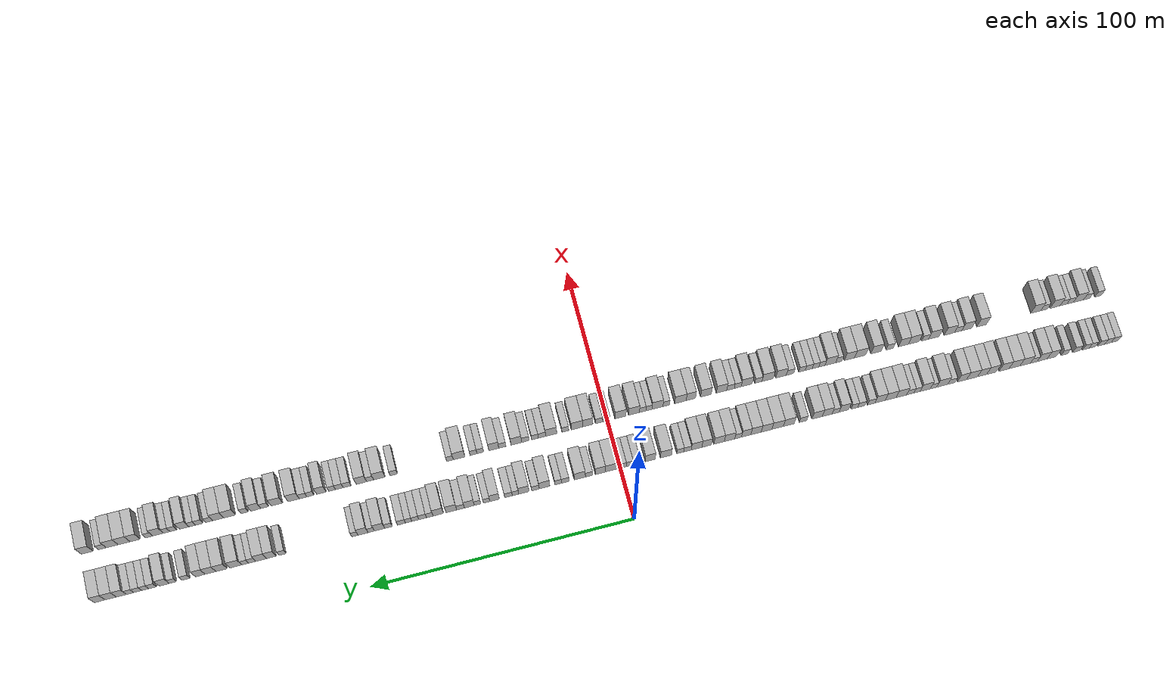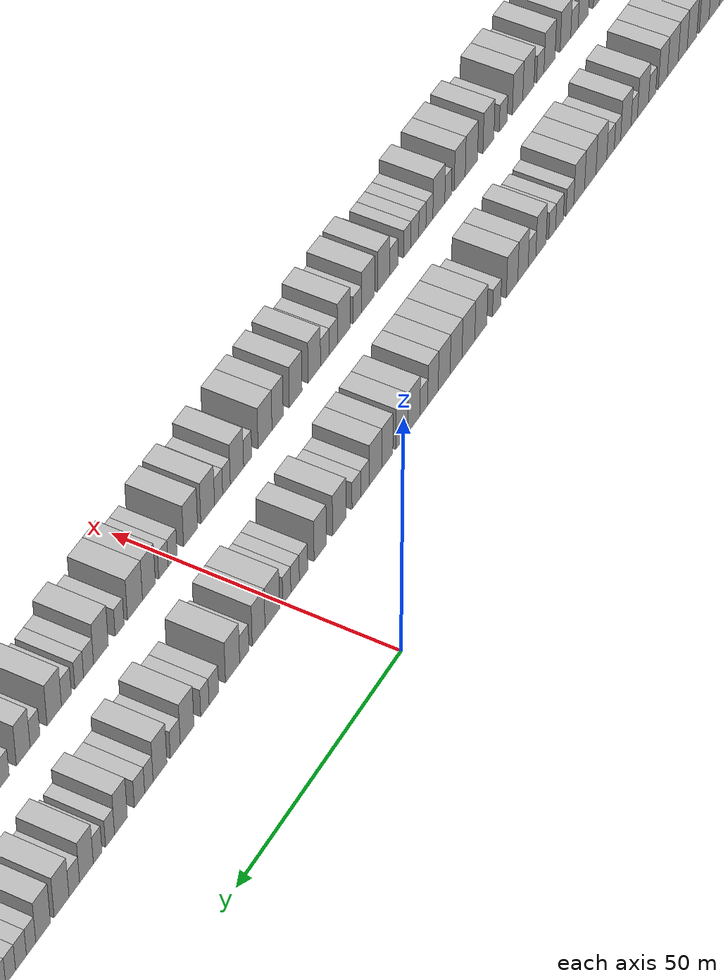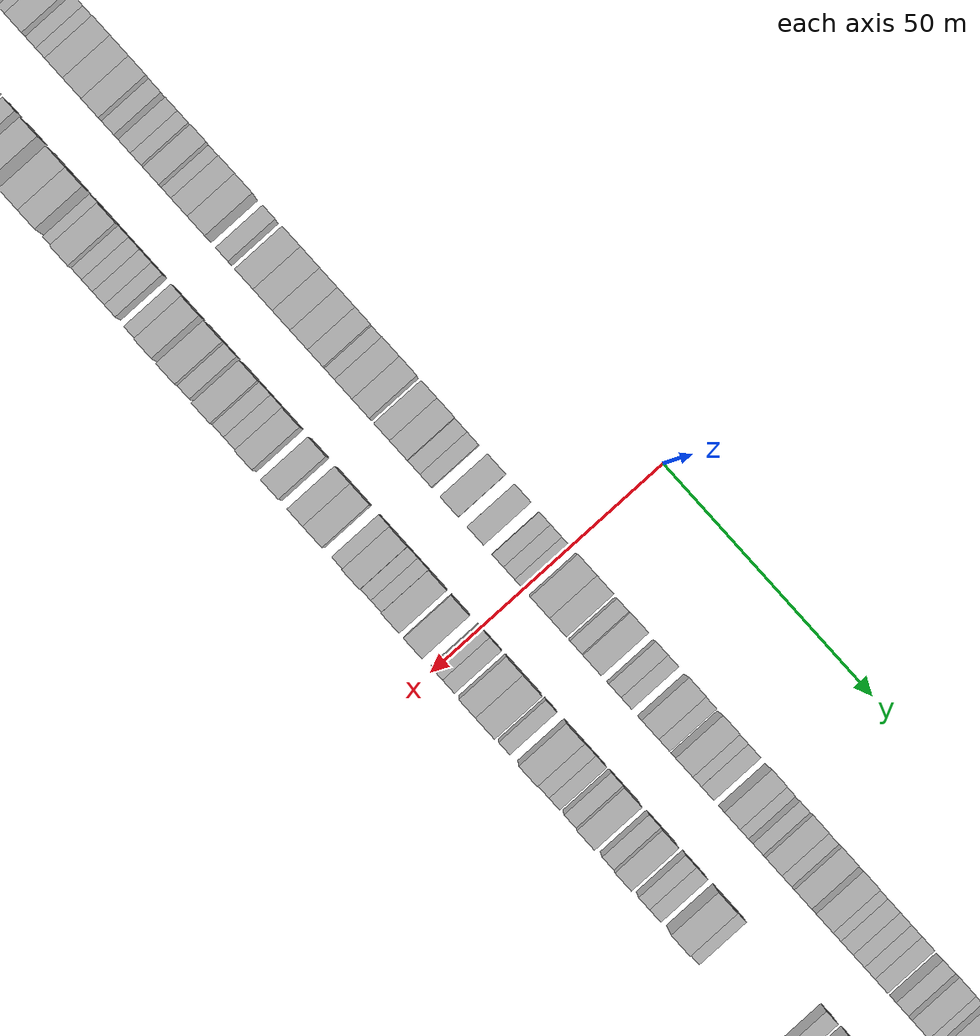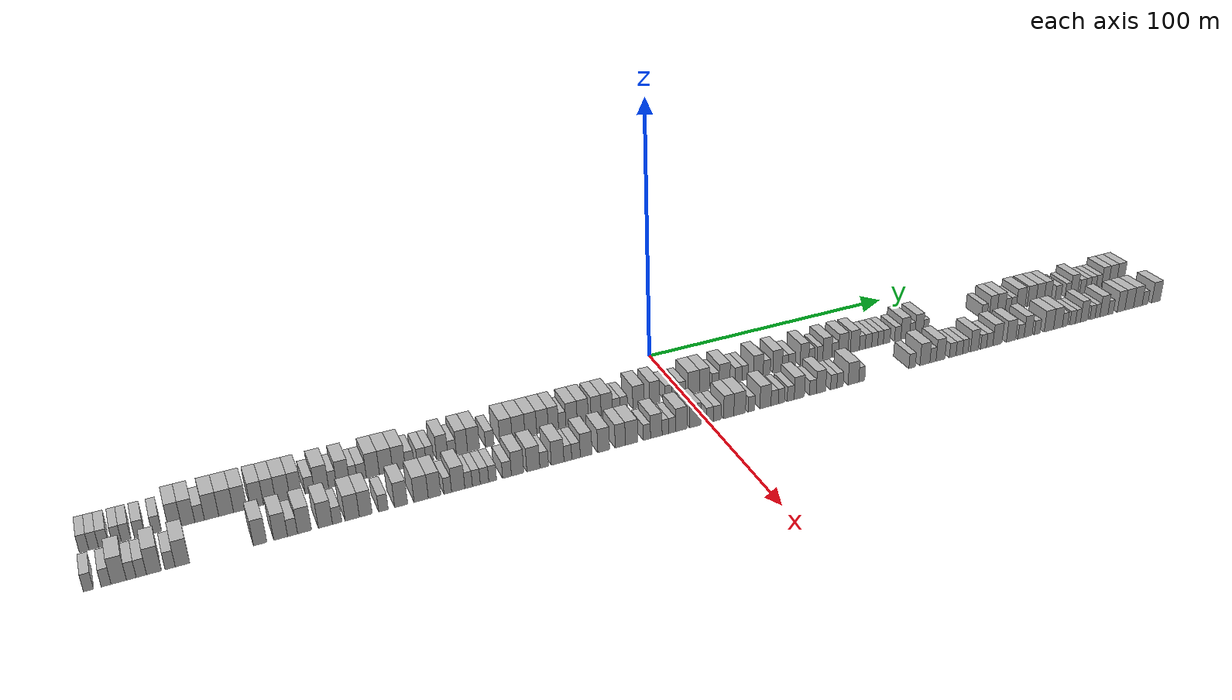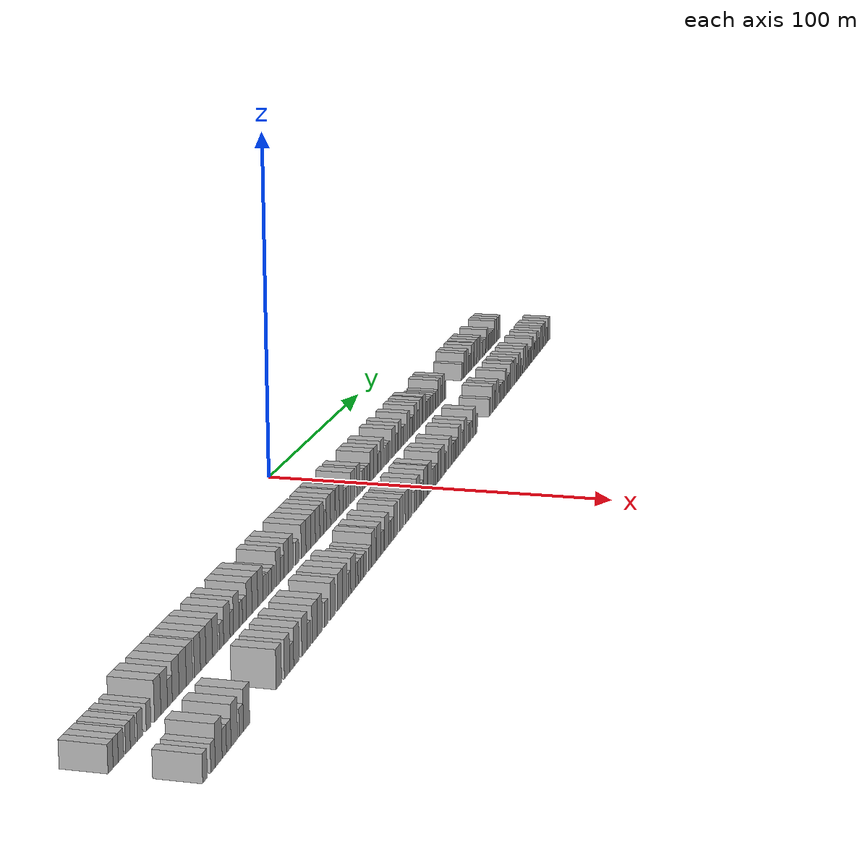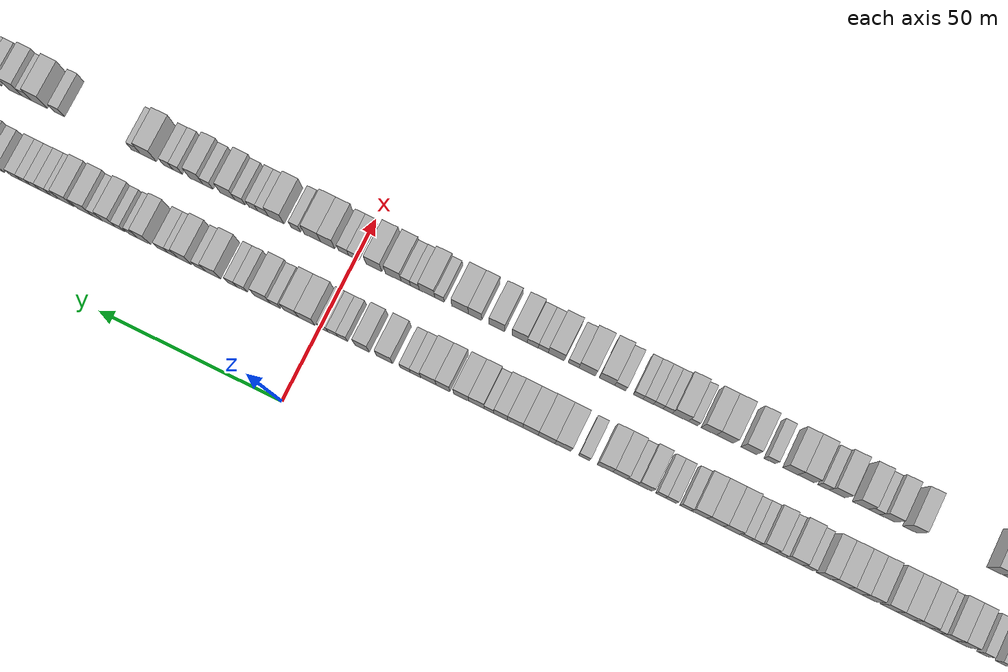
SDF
<sdf version="1.6">
 <world name="default">
  <scene>
   <sky><clouds><speed>12</speed></clouds></sky>
   <ambient>0.4 0.4 0.4 1</ambient>
   <background>0.7 0.7 0.7 1</background>
   <shadows>1</shadows>
  </scene>
  <gravity>0 0 -9.8066</gravity>
  <magnetic_field>6e-06 2.3e-05 -4.2e-05</magnetic_field>
  <physics default="0" name="default_physics" type="ode">
   <ode>
    <solver>
     <type>quick</type>
     <iters>10</iters>
     <sor>1.0</sor>
     <use_dynamic_moi_rescaling>0</use_dynamic_moi_rescaling>
    </solver>
    <constraints>
     <cfm>0</cfm>
     <erp>0.2</erp>
     <contact_max_correcting_vel>100</contact_max_correcting_vel>
     <contact_surface_layer>0.001</contact_surface_layer>
    </constraints>
   </ode>
   <max_step_size>0.004</max_step_size>
   <real_time_factor>1</real_time_factor>
   <real_time_update_rate>250</real_time_update_rate>
  </physics>
  <light name="sun" type="directional">
   <pose>0 0 10 0 0 0</pose>
   <diffuse>0.8 0.8 0.8 1</diffuse>
   <specular>0.2 0.2 0.2 1</specular>
   <attenuation>
    <range>1000</range>
    <constant>0.9</constant>
    <linear>0.01</linear>
    <quadratic>0.001</quadratic>
   </attenuation>
   <direction>-0.5 0.1 -0.9</direction>
  </light>
  <model name="building_1">
   <static>1</static>
   <pose>25.0000 -194.6913 0 0.000000 0.000000 0.000000</pose>
   <link name="link">
    <pose>0 0 3.00 0 0 0</pose>
    <collision name="collision"><geometry><box><size>10.0000 2.6174 6.0000</size></box></geometry></collision>
    <visual name="visual">
     <cast_shadows>0</cast_shadows>
     <geometry><box><size>10.0000 2.6174 6.0000</size></box></geometry>
     <material>
      <script>
       <uri>model://HANNAS_wall/materials/scripts</uri>
       <uri>model://HANNAS_wall/materials/textures</uri>
       <name>vrc/HANNAS_wall</name>
      </script>
     </material>
    </visual>
   </link>
  </model>
  <model name="building_2">
   <static>1</static>
   <pose>25.0000 -192.0661 0 0.000000 0.000000 0.000000</pose>
   <link name="link">
    <pose>0 0 3.00 0 0 0</pose>
    <collision name="collision"><geometry><box><size>10.0000 2.6331 6.0000</size></box></geometry></collision>
    <visual name="visual">
     <cast_shadows>0</cast_shadows>
     <geometry><box><size>10.0000 2.6331 6.0000</size></box></geometry>
     <material>
      <script>
       <uri>model://HANNAS_wall/materials/scripts</uri>
       <uri>model://HANNAS_wall/materials/textures</uri>
       <name>vrc/HANNAS_wall</name>
      </script>
     </material>
    </visual>
   </link>
  </model>
  <model name="building_3">
   <static>1</static>
   <pose>25.0000 -189.3518 0 0.000000 0.000000 0.000000</pose>
   <link name="link">
    <pose>0 0 3.00 0 0 0</pose>
    <collision name="collision"><geometry><box><size>10.0000 2.7956 6.0000</size></box></geometry></collision>
    <visual name="visual">
     <cast_shadows>0</cast_shadows>
     <geometry><box><size>10.0000 2.7956 6.0000</size></box></geometry>
     <material>
      <script>
       <uri>model://HANNAS_wall/materials/scripts</uri>
       <uri>model://HANNAS_wall/materials/textures</uri>
       <name>vrc/HANNAS_wall</name>
      </script>
     </material>
    </visual>
   </link>
  </model>
  <model name="building_4">
   <static>1</static>
   <pose>25.0000 -185.7143 0 0.000000 0.000000 0.000000</pose>
   <link name="link">
    <pose>0 0 3.00 0 0 0</pose>
    <collision name="collision"><geometry><box><size>10.0000 2.4792 6.0000</size></box></geometry></collision>
    <visual name="visual">
     <cast_shadows>0</cast_shadows>
     <geometry><box><size>10.0000 2.4792 6.0000</size></box></geometry>
     <material>
      <script>
       <uri>model://HANNAS_wall/materials/scripts</uri>
       <uri>model://HANNAS_wall/materials/textures</uri>
       <name>vrc/HANNAS_wall</name>
      </script>
     </material>
    </visual>
   </link>
  </model>
  <model name="building_5">
   <static>1</static>
   <pose>25.0000 -183.1439 0 0.000000 0.000000 0.000000</pose>
   <link name="link">
    <pose>0 0 3.00 0 0 0</pose>
    <collision name="collision"><geometry><box><size>10.0000 2.6617 6.0000</size></box></geometry></collision>
    <visual name="visual">
     <cast_shadows>0</cast_shadows>
     <geometry><box><size>10.0000 2.6617 6.0000</size></box></geometry>
     <material>
      <script>
       <uri>model://HANNAS_wall/materials/scripts</uri>
       <uri>model://HANNAS_wall/materials/textures</uri>
       <name>vrc/HANNAS_wall</name>
      </script>
     </material>
    </visual>
   </link>
  </model>
  <model name="building_6">
   <static>1</static>
   <pose>25.0000 -179.3535 0 0.000000 0.000000 0.000000</pose>
   <link name="link">
    <pose>0 0 3.00 0 0 0</pose>
    <collision name="collision"><geometry><box><size>10.0000 2.9190 6.0000</size></box></geometry></collision>
    <visual name="visual">
     <cast_shadows>0</cast_shadows>
     <geometry><box><size>10.0000 2.9190 6.0000</size></box></geometry>
     <material>
      <script>
       <uri>model://HANNAS_wall/materials/scripts</uri>
       <uri>model://HANNAS_wall/materials/textures</uri>
       <name>vrc/HANNAS_wall</name>
      </script>
     </material>
    </visual>
   </link>
  </model>
  <model name="building_7">
   <static>1</static>
   <pose>25.0000 -174.5721 0 0.000000 0.000000 0.000000</pose>
   <link name="link">
    <pose>0 0 3.00 0 0 0</pose>
    <collision name="collision"><geometry><box><size>10.0000 2.6437 6.0000</size></box></geometry></collision>
    <visual name="visual">
     <cast_shadows>0</cast_shadows>
     <geometry><box><size>10.0000 2.6437 6.0000</size></box></geometry>
     <material>
      <script>
       <uri>model://HANNAS_wall/materials/scripts</uri>
       <uri>model://HANNAS_wall/materials/textures</uri>
       <name>vrc/HANNAS_wall</name>
      </script>
     </material>
    </visual>
   </link>
  </model>
  <model name="building_8">
   <static>1</static>
   <pose>25.0000 -169.4105 0 0.000000 0.000000 0.000000</pose>
   <link name="link">
    <pose>0 0 4.50 0 0 0</pose>
    <collision name="collision"><geometry><box><size>10.0000 3.6795 9.0000</size></box></geometry></collision>
    <visual name="visual">
     <cast_shadows>0</cast_shadows>
     <geometry><box><size>10.0000 3.6795 9.0000</size></box></geometry>
     <material>
      <script>
       <uri>model://HANNAS_wall/materials/scripts</uri>
       <uri>model://HANNAS_wall/materials/textures</uri>
       <name>vrc/HANNAS_wall</name>
      </script>
     </material>
    </visual>
   </link>
  </model>
  <model name="building_9">
   <static>1</static>
   <pose>25.0000 -165.6424 0 0.000000 0.000000 0.000000</pose>
   <link name="link">
    <pose>0 0 4.50 0 0 0</pose>
    <collision name="collision"><geometry><box><size>10.0000 3.8567 9.0000</size></box></geometry></collision>
    <visual name="visual">
     <cast_shadows>0</cast_shadows>
     <geometry><box><size>10.0000 3.8567 9.0000</size></box></geometry>
     <material>
      <script>
       <uri>model://HANNAS_wall/materials/scripts</uri>
       <uri>model://HANNAS_wall/materials/textures</uri>
       <name>vrc/HANNAS_wall</name>
      </script>
     </material>
    </visual>
   </link>
  </model>
  <model name="building_10">
   <static>1</static>
   <pose>25.0000 -162.3278 0 0.000000 0.000000 0.000000</pose>
   <link name="link">
    <pose>0 0 3.00 0 0 0</pose>
    <collision name="collision"><geometry><box><size>10.0000 2.7725 6.0000</size></box></geometry></collision>
    <visual name="visual">
     <cast_shadows>0</cast_shadows>
     <geometry><box><size>10.0000 2.7725 6.0000</size></box></geometry>
     <material>
      <script>
       <uri>model://HANNAS_wall/materials/scripts</uri>
       <uri>model://HANNAS_wall/materials/textures</uri>
       <name>vrc/HANNAS_wall</name>
      </script>
     </material>
    </visual>
   </link>
  </model>
  <model name="building_11">
   <static>1</static>
   <pose>25.0000 -158.8644 0 0.000000 0.000000 0.000000</pose>
   <link name="link">
    <pose>0 0 4.50 0 0 0</pose>
    <collision name="collision"><geometry><box><size>10.0000 4.1543 9.0000</size></box></geometry></collision>
    <visual name="visual">
     <cast_shadows>0</cast_shadows>
     <geometry><box><size>10.0000 4.1543 9.0000</size></box></geometry>
     <material>
      <script>
       <uri>model://HANNAS_wall/materials/scripts</uri>
       <uri>model://HANNAS_wall/materials/textures</uri>
       <name>vrc/HANNAS_wall</name>
      </script>
     </material>
    </visual>
   </link>
  </model>
  <model name="building_12">
   <static>1</static>
   <pose>25.0000 -154.6055 0 0.000000 0.000000 0.000000</pose>
   <link name="link">
    <pose>0 0 4.50 0 0 0</pose>
    <collision name="collision"><geometry><box><size>10.0000 4.3636 9.0000</size></box></geometry></collision>
    <visual name="visual">
     <cast_shadows>0</cast_shadows>
     <geometry><box><size>10.0000 4.3636 9.0000</size></box></geometry>
     <material>
      <script>
       <uri>model://HANNAS_wall/materials/scripts</uri>
       <uri>model://HANNAS_wall/materials/textures</uri>
       <name>vrc/HANNAS_wall</name>
      </script>
     </material>
    </visual>
   </link>
  </model>
  <model name="building_13">
   <static>1</static>
   <pose>25.0000 -150.4279 0 0.000000 0.000000 0.000000</pose>
   <link name="link">
    <pose>0 0 4.50 0 0 0</pose>
    <collision name="collision"><geometry><box><size>10.0000 3.9915 9.0000</size></box></geometry></collision>
    <visual name="visual">
     <cast_shadows>0</cast_shadows>
     <geometry><box><size>10.0000 3.9915 9.0000</size></box></geometry>
     <material>
      <script>
       <uri>model://HANNAS_wall/materials/scripts</uri>
       <uri>model://HANNAS_wall/materials/textures</uri>
       <name>vrc/HANNAS_wall</name>
      </script>
     </material>
    </visual>
   </link>
  </model>
  <model name="building_14">
   <static>1</static>
   <pose>25.0000 -145.4855 0 0.000000 0.000000 0.000000</pose>
   <link name="link">
    <pose>0 0 4.50 0 0 0</pose>
    <collision name="collision"><geometry><box><size>10.0000 3.8934 9.0000</size></box></geometry></collision>
    <visual name="visual">
     <cast_shadows>0</cast_shadows>
     <geometry><box><size>10.0000 3.8934 9.0000</size></box></geometry>
     <material>
      <script>
       <uri>model://HANNAS_wall/materials/scripts</uri>
       <uri>model://HANNAS_wall/materials/textures</uri>
       <name>vrc/HANNAS_wall</name>
      </script>
     </material>
    </visual>
   </link>
  </model>
  <model name="building_15">
   <static>1</static>
   <pose>25.0000 -141.7141 0 0.000000 0.000000 0.000000</pose>
   <link name="link">
    <pose>0 0 4.50 0 0 0</pose>
    <collision name="collision"><geometry><box><size>10.0000 3.6494 9.0000</size></box></geometry></collision>
    <visual name="visual">
     <cast_shadows>0</cast_shadows>
     <geometry><box><size>10.0000 3.6494 9.0000</size></box></geometry>
     <material>
      <script>
       <uri>model://HANNAS_wall/materials/scripts</uri>
       <uri>model://HANNAS_wall/materials/textures</uri>
       <name>vrc/HANNAS_wall</name>
      </script>
     </material>
    </visual>
   </link>
  </model>
  <model name="building_16">
   <static>1</static>
   <pose>25.0000 -137.7262 0 0.000000 0.000000 0.000000</pose>
   <link name="link">
    <pose>0 0 4.50 0 0 0</pose>
    <collision name="collision"><geometry><box><size>10.0000 4.3263 9.0000</size></box></geometry></collision>
    <visual name="visual">
     <cast_shadows>0</cast_shadows>
     <geometry><box><size>10.0000 4.3263 9.0000</size></box></geometry>
     <material>
      <script>
       <uri>model://HANNAS_wall/materials/scripts</uri>
       <uri>model://HANNAS_wall/materials/textures</uri>
       <name>vrc/HANNAS_wall</name>
      </script>
     </material>
    </visual>
   </link>
  </model>
  <model name="building_17">
   <static>1</static>
   <pose>25.0000 -133.7458 0 0.000000 0.000000 0.000000</pose>
   <link name="link">
    <pose>0 0 4.50 0 0 0</pose>
    <collision name="collision"><geometry><box><size>10.0000 3.6346 9.0000</size></box></geometry></collision>
    <visual name="visual">
     <cast_shadows>0</cast_shadows>
     <geometry><box><size>10.0000 3.6346 9.0000</size></box></geometry>
     <material>
      <script>
       <uri>model://HANNAS_wall/materials/scripts</uri>
       <uri>model://HANNAS_wall/materials/textures</uri>
       <name>vrc/HANNAS_wall</name>
      </script>
     </material>
    </visual>
   </link>
  </model>
  <model name="building_18">
   <static>1</static>
   <pose>25.0000 -129.4912 0 0.000000 0.000000 0.000000</pose>
   <link name="link">
    <pose>0 0 3.00 0 0 0</pose>
    <collision name="collision"><geometry><box><size>10.0000 2.8746 6.0000</size></box></geometry></collision>
    <visual name="visual">
     <cast_shadows>0</cast_shadows>
     <geometry><box><size>10.0000 2.8746 6.0000</size></box></geometry>
     <material>
      <script>
       <uri>model://HANNAS_wall/materials/scripts</uri>
       <uri>model://HANNAS_wall/materials/textures</uri>
       <name>vrc/HANNAS_wall</name>
      </script>
     </material>
    </visual>
   </link>
  </model>
  <model name="building_19">
   <static>1</static>
   <pose>25.0000 -125.8565 0 0.000000 0.000000 0.000000</pose>
   <link name="link">
    <pose>0 0 4.50 0 0 0</pose>
    <collision name="collision"><geometry><box><size>10.0000 4.3947 9.0000</size></box></geometry></collision>
    <visual name="visual">
     <cast_shadows>0</cast_shadows>
     <geometry><box><size>10.0000 4.3947 9.0000</size></box></geometry>
     <material>
      <script>
       <uri>model://HANNAS_wall/materials/scripts</uri>
       <uri>model://HANNAS_wall/materials/textures</uri>
       <name>vrc/HANNAS_wall</name>
      </script>
     </material>
    </visual>
   </link>
  </model>
  <model name="building_20">
   <static>1</static>
   <pose>25.0000 -122.4116 0 0.000000 0.000000 0.000000</pose>
   <link name="link">
    <pose>0 0 3.00 0 0 0</pose>
    <collision name="collision"><geometry><box><size>10.0000 2.4952 6.0000</size></box></geometry></collision>
    <visual name="visual">
     <cast_shadows>0</cast_shadows>
     <geometry><box><size>10.0000 2.4952 6.0000</size></box></geometry>
     <material>
      <script>
       <uri>model://HANNAS_wall/materials/scripts</uri>
       <uri>model://HANNAS_wall/materials/textures</uri>
       <name>vrc/HANNAS_wall</name>
      </script>
     </material>
    </visual>
   </link>
  </model>
  <model name="building_21">
   <static>1</static>
   <pose>25.0000 -119.1423 0 0.000000 0.000000 0.000000</pose>
   <link name="link">
    <pose>0 0 4.50 0 0 0</pose>
    <collision name="collision"><geometry><box><size>10.0000 4.0435 9.0000</size></box></geometry></collision>
    <visual name="visual">
     <cast_shadows>0</cast_shadows>
     <geometry><box><size>10.0000 4.0435 9.0000</size></box></geometry>
     <material>
      <script>
       <uri>model://HANNAS_wall/materials/scripts</uri>
       <uri>model://HANNAS_wall/materials/textures</uri>
       <name>vrc/HANNAS_wall</name>
      </script>
     </material>
    </visual>
   </link>
  </model>
  <model name="building_22">
   <static>1</static>
   <pose>25.0000 -115.8984 0 0.000000 0.000000 0.000000</pose>
   <link name="link">
    <pose>0 0 3.00 0 0 0</pose>
    <collision name="collision"><geometry><box><size>10.0000 2.4443 6.0000</size></box></geometry></collision>
    <visual name="visual">
     <cast_shadows>0</cast_shadows>
     <geometry><box><size>10.0000 2.4443 6.0000</size></box></geometry>
     <material>
      <script>
       <uri>model://HANNAS_wall/materials/scripts</uri>
       <uri>model://HANNAS_wall/materials/textures</uri>
       <name>vrc/HANNAS_wall</name>
      </script>
     </material>
    </visual>
   </link>
  </model>
  <model name="building_23">
   <static>1</static>
   <pose>25.0000 -113.2176 0 0.000000 0.000000 0.000000</pose>
   <link name="link">
    <pose>0 0 3.00 0 0 0</pose>
    <collision name="collision"><geometry><box><size>10.0000 2.9173 6.0000</size></box></geometry></collision>
    <visual name="visual">
     <cast_shadows>0</cast_shadows>
     <geometry><box><size>10.0000 2.9173 6.0000</size></box></geometry>
     <material>
      <script>
       <uri>model://HANNAS_wall/materials/scripts</uri>
       <uri>model://HANNAS_wall/materials/textures</uri>
       <name>vrc/HANNAS_wall</name>
      </script>
     </material>
    </visual>
   </link>
  </model>
  <model name="building_24">
   <static>1</static>
   <pose>25.0000 -109.6810 0 0.000000 0.000000 0.000000</pose>
   <link name="link">
    <pose>0 0 4.50 0 0 0</pose>
    <collision name="collision"><geometry><box><size>10.0000 4.1557 9.0000</size></box></geometry></collision>
    <visual name="visual">
     <cast_shadows>0</cast_shadows>
     <geometry><box><size>10.0000 4.1557 9.0000</size></box></geometry>
     <material>
      <script>
       <uri>model://HANNAS_wall/materials/scripts</uri>
       <uri>model://HANNAS_wall/materials/textures</uri>
       <name>vrc/HANNAS_wall</name>
      </script>
     </material>
    </visual>
   </link>
  </model>
  <model name="building_25">
   <static>1</static>
   <pose>25.0000 -105.4493 0 0.000000 0.000000 0.000000</pose>
   <link name="link">
    <pose>0 0 4.50 0 0 0</pose>
    <collision name="collision"><geometry><box><size>10.0000 4.3079 9.0000</size></box></geometry></collision>
    <visual name="visual">
     <cast_shadows>0</cast_shadows>
     <geometry><box><size>10.0000 4.3079 9.0000</size></box></geometry>
     <material>
      <script>
       <uri>model://HANNAS_wall/materials/scripts</uri>
       <uri>model://HANNAS_wall/materials/textures</uri>
       <name>vrc/HANNAS_wall</name>
      </script>
     </material>
    </visual>
   </link>
  </model>
  <model name="building_26">
   <static>1</static>
   <pose>25.0000 -101.2713 0 0.000000 0.000000 0.000000</pose>
   <link name="link">
    <pose>0 0 4.50 0 0 0</pose>
    <collision name="collision"><geometry><box><size>10.0000 4.0480 9.0000</size></box></geometry></collision>
    <visual name="visual">
     <cast_shadows>0</cast_shadows>
     <geometry><box><size>10.0000 4.0480 9.0000</size></box></geometry>
     <material>
      <script>
       <uri>model://HANNAS_wall/materials/scripts</uri>
       <uri>model://HANNAS_wall/materials/textures</uri>
       <name>vrc/HANNAS_wall</name>
      </script>
     </material>
    </visual>
   </link>
  </model>
  <model name="building_27">
   <static>1</static>
   <pose>25.0000 -97.7955 0 0.000000 0.000000 0.000000</pose>
   <link name="link">
    <pose>0 0 3.00 0 0 0</pose>
    <collision name="collision"><geometry><box><size>10.0000 2.9036 6.0000</size></box></geometry></collision>
    <visual name="visual">
     <cast_shadows>0</cast_shadows>
     <geometry><box><size>10.0000 2.9036 6.0000</size></box></geometry>
     <material>
      <script>
       <uri>model://HANNAS_wall/materials/scripts</uri>
       <uri>model://HANNAS_wall/materials/textures</uri>
       <name>vrc/HANNAS_wall</name>
      </script>
     </material>
    </visual>
   </link>
  </model>
  <model name="building_28">
   <static>1</static>
   <pose>25.0000 -93.9045 0 0.000000 0.000000 0.000000</pose>
   <link name="link">
    <pose>0 0 3.00 0 0 0</pose>
    <collision name="collision"><geometry><box><size>10.0000 2.8784 6.0000</size></box></geometry></collision>
    <visual name="visual">
     <cast_shadows>0</cast_shadows>
     <geometry><box><size>10.0000 2.8784 6.0000</size></box></geometry>
     <material>
      <script>
       <uri>model://HANNAS_wall/materials/scripts</uri>
       <uri>model://HANNAS_wall/materials/textures</uri>
       <name>vrc/HANNAS_wall</name>
      </script>
     </material>
    </visual>
   </link>
  </model>
  <model name="building_29">
   <static>1</static>
   <pose>25.0000 -91.1947 0 0.000000 0.000000 0.000000</pose>
   <link name="link">
    <pose>0 0 3.00 0 0 0</pose>
    <collision name="collision"><geometry><box><size>10.0000 2.5411 6.0000</size></box></geometry></collision>
    <visual name="visual">
     <cast_shadows>0</cast_shadows>
     <geometry><box><size>10.0000 2.5411 6.0000</size></box></geometry>
     <material>
      <script>
       <uri>model://HANNAS_wall/materials/scripts</uri>
       <uri>model://HANNAS_wall/materials/textures</uri>
       <name>vrc/HANNAS_wall</name>
      </script>
     </material>
    </visual>
   </link>
  </model>
  <model name="building_30">
   <static>1</static>
   <pose>25.0000 -87.0586 0 0.000000 0.000000 0.000000</pose>
   <link name="link">
    <pose>0 0 4.50 0 0 0</pose>
    <collision name="collision"><geometry><box><size>10.0000 3.7311 9.0000</size></box></geometry></collision>
    <visual name="visual">
     <cast_shadows>0</cast_shadows>
     <geometry><box><size>10.0000 3.7311 9.0000</size></box></geometry>
     <material>
      <script>
       <uri>model://HANNAS_wall/materials/scripts</uri>
       <uri>model://HANNAS_wall/materials/textures</uri>
       <name>vrc/HANNAS_wall</name>
      </script>
     </material>
    </visual>
   </link>
  </model>
  <model name="building_31">
   <static>1</static>
   <pose>25.0000 -83.7866 0 0.000000 0.000000 0.000000</pose>
   <link name="link">
    <pose>0 0 3.00 0 0 0</pose>
    <collision name="collision"><geometry><box><size>10.0000 2.8130 6.0000</size></box></geometry></collision>
    <visual name="visual">
     <cast_shadows>0</cast_shadows>
     <geometry><box><size>10.0000 2.8130 6.0000</size></box></geometry>
     <material>
      <script>
       <uri>model://HANNAS_wall/materials/scripts</uri>
       <uri>model://HANNAS_wall/materials/textures</uri>
       <name>vrc/HANNAS_wall</name>
      </script>
     </material>
    </visual>
   </link>
  </model>
  <model name="building_32">
   <static>1</static>
   <pose>25.0000 -80.4817 0 0.000000 0.000000 0.000000</pose>
   <link name="link">
    <pose>0 0 4.50 0 0 0</pose>
    <collision name="collision"><geometry><box><size>10.0000 3.7967 9.0000</size></box></geometry></collision>
    <visual name="visual">
     <cast_shadows>0</cast_shadows>
     <geometry><box><size>10.0000 3.7967 9.0000</size></box></geometry>
     <material>
      <script>
       <uri>model://HANNAS_wall/materials/scripts</uri>
       <uri>model://HANNAS_wall/materials/textures</uri>
       <name>vrc/HANNAS_wall</name>
      </script>
     </material>
    </visual>
   </link>
  </model>
  <model name="building_33">
   <static>1</static>
   <pose>25.0000 -76.5333 0 0.000000 0.000000 0.000000</pose>
   <link name="link">
    <pose>0 0 4.50 0 0 0</pose>
    <collision name="collision"><geometry><box><size>10.0000 4.1000 9.0000</size></box></geometry></collision>
    <visual name="visual">
     <cast_shadows>0</cast_shadows>
     <geometry><box><size>10.0000 4.1000 9.0000</size></box></geometry>
     <material>
      <script>
       <uri>model://HANNAS_wall/materials/scripts</uri>
       <uri>model://HANNAS_wall/materials/textures</uri>
       <name>vrc/HANNAS_wall</name>
      </script>
     </material>
    </visual>
   </link>
  </model>
  <model name="building_34">
   <static>1</static>
   <pose>25.0000 -71.0130 0 0.000000 0.000000 0.000000</pose>
   <link name="link">
    <pose>0 0 3.00 0 0 0</pose>
    <collision name="collision"><geometry><box><size>10.0000 2.9405 6.0000</size></box></geometry></collision>
    <visual name="visual">
     <cast_shadows>0</cast_shadows>
     <geometry><box><size>10.0000 2.9405 6.0000</size></box></geometry>
     <material>
      <script>
       <uri>model://HANNAS_wall/materials/scripts</uri>
       <uri>model://HANNAS_wall/materials/textures</uri>
       <name>vrc/HANNAS_wall</name>
      </script>
     </material>
    </visual>
   </link>
  </model>
  <model name="building_35">
   <static>1</static>
   <pose>25.0000 -65.4058 0 0.000000 0.000000 0.000000</pose>
   <link name="link">
    <pose>0 0 4.50 0 0 0</pose>
    <collision name="collision"><geometry><box><size>10.0000 4.2739 9.0000</size></box></geometry></collision>
    <visual name="visual">
     <cast_shadows>0</cast_shadows>
     <geometry><box><size>10.0000 4.2739 9.0000</size></box></geometry>
     <material>
      <script>
       <uri>model://HANNAS_wall/materials/scripts</uri>
       <uri>model://HANNAS_wall/materials/textures</uri>
       <name>vrc/HANNAS_wall</name>
      </script>
     </material>
    </visual>
   </link>
  </model>
  <model name="building_36">
   <static>1</static>
   <pose>25.0000 -61.0355 0 0.000000 0.000000 0.000000</pose>
   <link name="link">
    <pose>0 0 4.50 0 0 0</pose>
    <collision name="collision"><geometry><box><size>10.0000 4.4668 9.0000</size></box></geometry></collision>
    <visual name="visual">
     <cast_shadows>0</cast_shadows>
     <geometry><box><size>10.0000 4.4668 9.0000</size></box></geometry>
     <material>
      <script>
       <uri>model://HANNAS_wall/materials/scripts</uri>
       <uri>model://HANNAS_wall/materials/textures</uri>
       <name>vrc/HANNAS_wall</name>
      </script>
     </material>
    </visual>
   </link>
  </model>
  <model name="building_37">
   <static>1</static>
   <pose>25.0000 -56.7351 0 0.000000 0.000000 0.000000</pose>
   <link name="link">
    <pose>0 0 4.50 0 0 0</pose>
    <collision name="collision"><geometry><box><size>10.0000 4.1340 9.0000</size></box></geometry></collision>
    <visual name="visual">
     <cast_shadows>0</cast_shadows>
     <geometry><box><size>10.0000 4.1340 9.0000</size></box></geometry>
     <material>
      <script>
       <uri>model://HANNAS_wall/materials/scripts</uri>
       <uri>model://HANNAS_wall/materials/textures</uri>
       <name>vrc/HANNAS_wall</name>
      </script>
     </material>
    </visual>
   </link>
  </model>
  <model name="building_38">
   <static>1</static>
   <pose>25.0000 -52.6220 0 0.000000 0.000000 0.000000</pose>
   <link name="link">
    <pose>0 0 4.50 0 0 0</pose>
    <collision name="collision"><geometry><box><size>10.0000 4.0922 9.0000</size></box></geometry></collision>
    <visual name="visual">
     <cast_shadows>0</cast_shadows>
     <geometry><box><size>10.0000 4.0922 9.0000</size></box></geometry>
     <material>
      <script>
       <uri>model://HANNAS_wall/materials/scripts</uri>
       <uri>model://HANNAS_wall/materials/textures</uri>
       <name>vrc/HANNAS_wall</name>
      </script>
     </material>
    </visual>
   </link>
  </model>
  <model name="building_39">
   <static>1</static>
   <pose>25.0000 -48.7673 0 0.000000 0.000000 0.000000</pose>
   <link name="link">
    <pose>0 0 4.50 0 0 0</pose>
    <collision name="collision"><geometry><box><size>10.0000 3.6170 9.0000</size></box></geometry></collision>
    <visual name="visual">
     <cast_shadows>0</cast_shadows>
     <geometry><box><size>10.0000 3.6170 9.0000</size></box></geometry>
     <material>
      <script>
       <uri>model://HANNAS_wall/materials/scripts</uri>
       <uri>model://HANNAS_wall/materials/textures</uri>
       <name>vrc/HANNAS_wall</name>
      </script>
     </material>
    </visual>
   </link>
  </model>
  <model name="building_40">
   <static>1</static>
   <pose>25.0000 -45.6345 0 0.000000 0.000000 0.000000</pose>
   <link name="link">
    <pose>0 0 3.00 0 0 0</pose>
    <collision name="collision"><geometry><box><size>10.0000 2.6487 6.0000</size></box></geometry></collision>
    <visual name="visual">
     <cast_shadows>0</cast_shadows>
     <geometry><box><size>10.0000 2.6487 6.0000</size></box></geometry>
     <material>
      <script>
       <uri>model://HANNAS_wall/materials/scripts</uri>
       <uri>model://HANNAS_wall/materials/textures</uri>
       <name>vrc/HANNAS_wall</name>
      </script>
     </material>
    </visual>
   </link>
  </model>
  <model name="building_41">
   <static>1</static>
   <pose>25.0000 -42.2691 0 0.000000 0.000000 0.000000</pose>
   <link name="link">
    <pose>0 0 4.50 0 0 0</pose>
    <collision name="collision"><geometry><box><size>10.0000 4.0822 9.0000</size></box></geometry></collision>
    <visual name="visual">
     <cast_shadows>0</cast_shadows>
     <geometry><box><size>10.0000 4.0822 9.0000</size></box></geometry>
     <material>
      <script>
       <uri>model://HANNAS_wall/materials/scripts</uri>
       <uri>model://HANNAS_wall/materials/textures</uri>
       <name>vrc/HANNAS_wall</name>
      </script>
     </material>
    </visual>
   </link>
  </model>
  <model name="building_42">
   <static>1</static>
   <pose>25.0000 -38.2107 0 0.000000 0.000000 0.000000</pose>
   <link name="link">
    <pose>0 0 4.50 0 0 0</pose>
    <collision name="collision"><geometry><box><size>10.0000 4.0345 9.0000</size></box></geometry></collision>
    <visual name="visual">
     <cast_shadows>0</cast_shadows>
     <geometry><box><size>10.0000 4.0345 9.0000</size></box></geometry>
     <material>
      <script>
       <uri>model://HANNAS_wall/materials/scripts</uri>
       <uri>model://HANNAS_wall/materials/textures</uri>
       <name>vrc/HANNAS_wall</name>
      </script>
     </material>
    </visual>
   </link>
  </model>
  <model name="building_43">
   <static>1</static>
   <pose>25.0000 -33.3450 0 0.000000 0.000000 0.000000</pose>
   <link name="link">
    <pose>0 0 4.50 0 0 0</pose>
    <collision name="collision"><geometry><box><size>10.0000 3.6970 9.0000</size></box></geometry></collision>
    <visual name="visual">
     <cast_shadows>0</cast_shadows>
     <geometry><box><size>10.0000 3.6970 9.0000</size></box></geometry>
     <material>
      <script>
       <uri>model://HANNAS_wall/materials/scripts</uri>
       <uri>model://HANNAS_wall/materials/textures</uri>
       <name>vrc/HANNAS_wall</name>
      </script>
     </material>
    </visual>
   </link>
  </model>
  <model name="building_44">
   <static>1</static>
   <pose>25.0000 -29.4401 0 0.000000 0.000000 0.000000</pose>
   <link name="link">
    <pose>0 0 4.50 0 0 0</pose>
    <collision name="collision"><geometry><box><size>10.0000 4.1129 9.0000</size></box></geometry></collision>
    <visual name="visual">
     <cast_shadows>0</cast_shadows>
     <geometry><box><size>10.0000 4.1129 9.0000</size></box></geometry>
     <material>
      <script>
       <uri>model://HANNAS_wall/materials/scripts</uri>
       <uri>model://HANNAS_wall/materials/textures</uri>
       <name>vrc/HANNAS_wall</name>
      </script>
     </material>
    </visual>
   </link>
  </model>
  <model name="building_45">
   <static>1</static>
   <pose>25.0000 -25.9536 0 0.000000 0.000000 0.000000</pose>
   <link name="link">
    <pose>0 0 3.00 0 0 0</pose>
    <collision name="collision"><geometry><box><size>10.0000 2.8602 6.0000</size></box></geometry></collision>
    <visual name="visual">
     <cast_shadows>0</cast_shadows>
     <geometry><box><size>10.0000 2.8602 6.0000</size></box></geometry>
     <material>
      <script>
       <uri>model://HANNAS_wall/materials/scripts</uri>
       <uri>model://HANNAS_wall/materials/textures</uri>
       <name>vrc/HANNAS_wall</name>
      </script>
     </material>
    </visual>
   </link>
  </model>
  <model name="building_46">
   <static>1</static>
   <pose>25.0000 -23.1433 0 0.000000 0.000000 0.000000</pose>
   <link name="link">
    <pose>0 0 3.00 0 0 0</pose>
    <collision name="collision"><geometry><box><size>10.0000 2.7603 6.0000</size></box></geometry></collision>
    <visual name="visual">
     <cast_shadows>0</cast_shadows>
     <geometry><box><size>10.0000 2.7603 6.0000</size></box></geometry>
     <material>
      <script>
       <uri>model://HANNAS_wall/materials/scripts</uri>
       <uri>model://HANNAS_wall/materials/textures</uri>
       <name>vrc/HANNAS_wall</name>
      </script>
     </material>
    </visual>
   </link>
  </model>
  <model name="building_47">
   <static>1</static>
   <pose>25.0000 -17.6112 0 0.000000 0.000000 0.000000</pose>
   <link name="link">
    <pose>0 0 4.50 0 0 0</pose>
    <collision name="collision"><geometry><box><size>10.0000 4.3039 9.0000</size></box></geometry></collision>
    <visual name="visual">
     <cast_shadows>0</cast_shadows>
     <geometry><box><size>10.0000 4.3039 9.0000</size></box></geometry>
     <material>
      <script>
       <uri>model://HANNAS_wall/materials/scripts</uri>
       <uri>model://HANNAS_wall/materials/textures</uri>
       <name>vrc/HANNAS_wall</name>
      </script>
     </material>
    </visual>
   </link>
  </model>
  <model name="building_48">
   <static>1</static>
   <pose>25.0000 -11.5176 0 0.000000 0.000000 0.000000</pose>
   <link name="link">
    <pose>0 0 4.50 0 0 0</pose>
    <collision name="collision"><geometry><box><size>10.0000 3.8833 9.0000</size></box></geometry></collision>
    <visual name="visual">
     <cast_shadows>0</cast_shadows>
     <geometry><box><size>10.0000 3.8833 9.0000</size></box></geometry>
     <material>
      <script>
       <uri>model://HANNAS_wall/materials/scripts</uri>
       <uri>model://HANNAS_wall/materials/textures</uri>
       <name>vrc/HANNAS_wall</name>
      </script>
     </material>
    </visual>
   </link>
  </model>
  <model name="building_49">
   <static>1</static>
   <pose>25.0000 -6.2448 0 0.000000 0.000000 0.000000</pose>
   <link name="link">
    <pose>0 0 3.00 0 0 0</pose>
    <collision name="collision"><geometry><box><size>10.0000 2.6624 6.0000</size></box></geometry></collision>
    <visual name="visual">
     <cast_shadows>0</cast_shadows>
     <geometry><box><size>10.0000 2.6624 6.0000</size></box></geometry>
     <material>
      <script>
       <uri>model://HANNAS_wall/materials/scripts</uri>
       <uri>model://HANNAS_wall/materials/textures</uri>
       <name>vrc/HANNAS_wall</name>
      </script>
     </material>
    </visual>
   </link>
  </model>
  <model name="building_50">
   <static>1</static>
   <pose>25.0000 -3.5870 0 0.000000 0.000000 0.000000</pose>
   <link name="link">
    <pose>0 0 3.00 0 0 0</pose>
    <collision name="collision"><geometry><box><size>10.0000 2.6531 6.0000</size></box></geometry></collision>
    <visual name="visual">
     <cast_shadows>0</cast_shadows>
     <geometry><box><size>10.0000 2.6531 6.0000</size></box></geometry>
     <material>
      <script>
       <uri>model://HANNAS_wall/materials/scripts</uri>
       <uri>model://HANNAS_wall/materials/textures</uri>
       <name>vrc/HANNAS_wall</name>
      </script>
     </material>
    </visual>
   </link>
  </model>
  <model name="building_51">
   <static>1</static>
   <pose>25.0000 -0.9893 0 0.000000 0.000000 0.000000</pose>
   <link name="link">
    <pose>0 0 3.00 0 0 0</pose>
    <collision name="collision"><geometry><box><size>10.0000 2.5422 6.0000</size></box></geometry></collision>
    <visual name="visual">
     <cast_shadows>0</cast_shadows>
     <geometry><box><size>10.0000 2.5422 6.0000</size></box></geometry>
     <material>
      <script>
       <uri>model://HANNAS_wall/materials/scripts</uri>
       <uri>model://HANNAS_wall/materials/textures</uri>
       <name>vrc/HANNAS_wall</name>
      </script>
     </material>
    </visual>
   </link>
  </model>
  <model name="building_52">
   <static>1</static>
   <pose>25.0000 3.5239 0 0.000000 0.000000 0.000000</pose>
   <link name="link">
    <pose>0 0 4.50 0 0 0</pose>
    <collision name="collision"><geometry><box><size>10.0000 4.4843 9.0000</size></box></geometry></collision>
    <visual name="visual">
     <cast_shadows>0</cast_shadows>
     <geometry><box><size>10.0000 4.4843 9.0000</size></box></geometry>
     <material>
      <script>
       <uri>model://HANNAS_wall/materials/scripts</uri>
       <uri>model://HANNAS_wall/materials/textures</uri>
       <name>vrc/HANNAS_wall</name>
      </script>
     </material>
    </visual>
   </link>
  </model>
  <model name="building_53">
   <static>1</static>
   <pose>25.0000 7.7307 0 0.000000 0.000000 0.000000</pose>
   <link name="link">
    <pose>0 0 4.50 0 0 0</pose>
    <collision name="collision"><geometry><box><size>10.0000 3.9293 9.0000</size></box></geometry></collision>
    <visual name="visual">
     <cast_shadows>0</cast_shadows>
     <geometry><box><size>10.0000 3.9293 9.0000</size></box></geometry>
     <material>
      <script>
       <uri>model://HANNAS_wall/materials/scripts</uri>
       <uri>model://HANNAS_wall/materials/textures</uri>
       <name>vrc/HANNAS_wall</name>
      </script>
     </material>
    </visual>
   </link>
  </model>
  <model name="building_54">
   <static>1</static>
   <pose>25.0000 12.1050 0 0.000000 0.000000 0.000000</pose>
   <link name="link">
    <pose>0 0 3.00 0 0 0</pose>
    <collision name="collision"><geometry><box><size>10.0000 2.8193 6.0000</size></box></geometry></collision>
    <visual name="visual">
     <cast_shadows>0</cast_shadows>
     <geometry><box><size>10.0000 2.8193 6.0000</size></box></geometry>
     <material>
      <script>
       <uri>model://HANNAS_wall/materials/scripts</uri>
       <uri>model://HANNAS_wall/materials/textures</uri>
       <name>vrc/HANNAS_wall</name>
      </script>
     </material>
    </visual>
   </link>
  </model>
  <model name="building_55">
   <static>1</static>
   <pose>25.0000 15.6615 0 0.000000 0.000000 0.000000</pose>
   <link name="link">
    <pose>0 0 4.50 0 0 0</pose>
    <collision name="collision"><geometry><box><size>10.0000 4.2938 9.0000</size></box></geometry></collision>
    <visual name="visual">
     <cast_shadows>0</cast_shadows>
     <geometry><box><size>10.0000 4.2938 9.0000</size></box></geometry>
     <material>
      <script>
       <uri>model://HANNAS_wall/materials/scripts</uri>
       <uri>model://HANNAS_wall/materials/textures</uri>
       <name>vrc/HANNAS_wall</name>
      </script>
     </material>
    </visual>
   </link>
  </model>
  <model name="building_56">
   <static>1</static>
   <pose>25.0000 21.2589 0 0.000000 0.000000 0.000000</pose>
   <link name="link">
    <pose>0 0 3.00 0 0 0</pose>
    <collision name="collision"><geometry><box><size>10.0000 2.9010 6.0000</size></box></geometry></collision>
    <visual name="visual">
     <cast_shadows>0</cast_shadows>
     <geometry><box><size>10.0000 2.9010 6.0000</size></box></geometry>
     <material>
      <script>
       <uri>model://HANNAS_wall/materials/scripts</uri>
       <uri>model://HANNAS_wall/materials/textures</uri>
       <name>vrc/HANNAS_wall</name>
      </script>
     </material>
    </visual>
   </link>
  </model>
  <model name="building_57">
   <static>1</static>
   <pose>25.0000 23.9494 0 0.000000 0.000000 0.000000</pose>
   <link name="link">
    <pose>0 0 3.00 0 0 0</pose>
    <collision name="collision"><geometry><box><size>10.0000 2.4800 6.0000</size></box></geometry></collision>
    <visual name="visual">
     <cast_shadows>0</cast_shadows>
     <geometry><box><size>10.0000 2.4800 6.0000</size></box></geometry>
     <material>
      <script>
       <uri>model://HANNAS_wall/materials/scripts</uri>
       <uri>model://HANNAS_wall/materials/textures</uri>
       <name>vrc/HANNAS_wall</name>
      </script>
     </material>
    </visual>
   </link>
  </model>
  <model name="building_58">
   <static>1</static>
   <pose>25.0000 29.2018 0 0.000000 0.000000 0.000000</pose>
   <link name="link">
    <pose>0 0 4.50 0 0 0</pose>
    <collision name="collision"><geometry><box><size>10.0000 4.0249 9.0000</size></box></geometry></collision>
    <visual name="visual">
     <cast_shadows>0</cast_shadows>
     <geometry><box><size>10.0000 4.0249 9.0000</size></box></geometry>
     <material>
      <script>
       <uri>model://HANNAS_wall/materials/scripts</uri>
       <uri>model://HANNAS_wall/materials/textures</uri>
       <name>vrc/HANNAS_wall</name>
      </script>
     </material>
    </visual>
   </link>
  </model>
  <model name="building_59">
   <static>1</static>
   <pose>25.0000 32.6660 0 0.000000 0.000000 0.000000</pose>
   <link name="link">
    <pose>0 0 3.00 0 0 0</pose>
    <collision name="collision"><geometry><box><size>10.0000 2.9033 6.0000</size></box></geometry></collision>
    <visual name="visual">
     <cast_shadows>0</cast_shadows>
     <geometry><box><size>10.0000 2.9033 6.0000</size></box></geometry>
     <material>
      <script>
       <uri>model://HANNAS_wall/materials/scripts</uri>
       <uri>model://HANNAS_wall/materials/textures</uri>
       <name>vrc/HANNAS_wall</name>
      </script>
     </material>
    </visual>
   </link>
  </model>
  <model name="building_60">
   <static>1</static>
   <pose>25.0000 37.1094 0 0.000000 0.000000 0.000000</pose>
   <link name="link">
    <pose>0 0 4.50 0 0 0</pose>
    <collision name="collision"><geometry><box><size>10.0000 3.9836 9.0000</size></box></geometry></collision>
    <visual name="visual">
     <cast_shadows>0</cast_shadows>
     <geometry><box><size>10.0000 3.9836 9.0000</size></box></geometry>
     <material>
      <script>
       <uri>model://HANNAS_wall/materials/scripts</uri>
       <uri>model://HANNAS_wall/materials/textures</uri>
       <name>vrc/HANNAS_wall</name>
      </script>
     </material>
    </visual>
   </link>
  </model>
  <model name="building_61">
   <static>1</static>
   <pose>25.0000 40.3164 0 0.000000 0.000000 0.000000</pose>
   <link name="link">
    <pose>0 0 3.00 0 0 0</pose>
    <collision name="collision"><geometry><box><size>10.0000 2.4304 6.0000</size></box></geometry></collision>
    <visual name="visual">
     <cast_shadows>0</cast_shadows>
     <geometry><box><size>10.0000 2.4304 6.0000</size></box></geometry>
     <material>
      <script>
       <uri>model://HANNAS_wall/materials/scripts</uri>
       <uri>model://HANNAS_wall/materials/textures</uri>
       <name>vrc/HANNAS_wall</name>
      </script>
     </material>
    </visual>
   </link>
  </model>
  <model name="building_62">
   <static>1</static>
   <pose>25.0000 43.0006 0 0.000000 0.000000 0.000000</pose>
   <link name="link">
    <pose>0 0 3.00 0 0 0</pose>
    <collision name="collision"><geometry><box><size>10.0000 2.9379 6.0000</size></box></geometry></collision>
    <visual name="visual">
     <cast_shadows>0</cast_shadows>
     <geometry><box><size>10.0000 2.9379 6.0000</size></box></geometry>
     <material>
      <script>
       <uri>model://HANNAS_wall/materials/scripts</uri>
       <uri>model://HANNAS_wall/materials/textures</uri>
       <name>vrc/HANNAS_wall</name>
      </script>
     </material>
    </visual>
   </link>
  </model>
  <model name="building_63">
   <static>1</static>
   <pose>25.0000 48.2834 0 0.000000 0.000000 0.000000</pose>
   <link name="link">
    <pose>0 0 4.50 0 0 0</pose>
    <collision name="collision"><geometry><box><size>10.0000 3.6277 9.0000</size></box></geometry></collision>
    <visual name="visual">
     <cast_shadows>0</cast_shadows>
     <geometry><box><size>10.0000 3.6277 9.0000</size></box></geometry>
     <material>
      <script>
       <uri>model://HANNAS_wall/materials/scripts</uri>
       <uri>model://HANNAS_wall/materials/textures</uri>
       <name>vrc/HANNAS_wall</name>
      </script>
     </material>
    </visual>
   </link>
  </model>
  <model name="building_64">
   <static>1</static>
   <pose>25.0000 51.3525 0 0.000000 0.000000 0.000000</pose>
   <link name="link">
    <pose>0 0 3.00 0 0 0</pose>
    <collision name="collision"><geometry><box><size>10.0000 2.5106 6.0000</size></box></geometry></collision>
    <visual name="visual">
     <cast_shadows>0</cast_shadows>
     <geometry><box><size>10.0000 2.5106 6.0000</size></box></geometry>
     <material>
      <script>
       <uri>model://HANNAS_wall/materials/scripts</uri>
       <uri>model://HANNAS_wall/materials/textures</uri>
       <name>vrc/HANNAS_wall</name>
      </script>
     </material>
    </visual>
   </link>
  </model>
  <model name="building_65">
   <static>1</static>
   <pose>25.0000 54.8151 0 0.000000 0.000000 0.000000</pose>
   <link name="link">
    <pose>0 0 3.00 0 0 0</pose>
    <collision name="collision"><geometry><box><size>10.0000 2.4147 6.0000</size></box></geometry></collision>
    <visual name="visual">
     <cast_shadows>0</cast_shadows>
     <geometry><box><size>10.0000 2.4147 6.0000</size></box></geometry>
     <material>
      <script>
       <uri>model://HANNAS_wall/materials/scripts</uri>
       <uri>model://HANNAS_wall/materials/textures</uri>
       <name>vrc/HANNAS_wall</name>
      </script>
     </material>
    </visual>
   </link>
  </model>
  <model name="building_66">
   <static>1</static>
   <pose>25.0000 57.9305 0 0.000000 0.000000 0.000000</pose>
   <link name="link">
    <pose>0 0 4.50 0 0 0</pose>
    <collision name="collision"><geometry><box><size>10.0000 3.8160 9.0000</size></box></geometry></collision>
    <visual name="visual">
     <cast_shadows>0</cast_shadows>
     <geometry><box><size>10.0000 3.8160 9.0000</size></box></geometry>
     <material>
      <script>
       <uri>model://HANNAS_wall/materials/scripts</uri>
       <uri>model://HANNAS_wall/materials/textures</uri>
       <name>vrc/HANNAS_wall</name>
      </script>
     </material>
    </visual>
   </link>
  </model>
  <model name="building_67">
   <static>1</static>
   <pose>25.0000 61.2913 0 0.000000 0.000000 0.000000</pose>
   <link name="link">
    <pose>0 0 3.00 0 0 0</pose>
    <collision name="collision"><geometry><box><size>10.0000 2.9056 6.0000</size></box></geometry></collision>
    <visual name="visual">
     <cast_shadows>0</cast_shadows>
     <geometry><box><size>10.0000 2.9056 6.0000</size></box></geometry>
     <material>
      <script>
       <uri>model://HANNAS_wall/materials/scripts</uri>
       <uri>model://HANNAS_wall/materials/textures</uri>
       <name>vrc/HANNAS_wall</name>
      </script>
     </material>
    </visual>
   </link>
  </model>
  <model name="building_68">
   <static>1</static>
   <pose>25.0000 64.7740 0 0.000000 0.000000 0.000000</pose>
   <link name="link">
    <pose>0 0 4.50 0 0 0</pose>
    <collision name="collision"><geometry><box><size>10.0000 4.0598 9.0000</size></box></geometry></collision>
    <visual name="visual">
     <cast_shadows>0</cast_shadows>
     <geometry><box><size>10.0000 4.0598 9.0000</size></box></geometry>
     <material>
      <script>
       <uri>model://HANNAS_wall/materials/scripts</uri>
       <uri>model://HANNAS_wall/materials/textures</uri>
       <name>vrc/HANNAS_wall</name>
      </script>
     </material>
    </visual>
   </link>
  </model>
  <model name="building_69">
   <static>1</static>
   <pose>25.0000 69.7808 0 0.000000 0.000000 0.000000</pose>
   <link name="link">
    <pose>0 0 4.50 0 0 0</pose>
    <collision name="collision"><geometry><box><size>10.0000 3.9539 9.0000</size></box></geometry></collision>
    <visual name="visual">
     <cast_shadows>0</cast_shadows>
     <geometry><box><size>10.0000 3.9539 9.0000</size></box></geometry>
     <material>
      <script>
       <uri>model://HANNAS_wall/materials/scripts</uri>
       <uri>model://HANNAS_wall/materials/textures</uri>
       <name>vrc/HANNAS_wall</name>
      </script>
     </material>
    </visual>
   </link>
  </model>
  <model name="building_70">
   <static>1</static>
   <pose>25.0000 73.0188 0 0.000000 0.000000 0.000000</pose>
   <link name="link">
    <pose>0 0 3.00 0 0 0</pose>
    <collision name="collision"><geometry><box><size>10.0000 2.5220 6.0000</size></box></geometry></collision>
    <visual name="visual">
     <cast_shadows>0</cast_shadows>
     <geometry><box><size>10.0000 2.5220 6.0000</size></box></geometry>
     <material>
      <script>
       <uri>model://HANNAS_wall/materials/scripts</uri>
       <uri>model://HANNAS_wall/materials/textures</uri>
       <name>vrc/HANNAS_wall</name>
      </script>
     </material>
    </visual>
   </link>
  </model>
  <model name="building_71">
   <static>1</static>
   <pose>25.0000 75.7211 0 0.000000 0.000000 0.000000</pose>
   <link name="link">
    <pose>0 0 3.00 0 0 0</pose>
    <collision name="collision"><geometry><box><size>10.0000 2.8826 6.0000</size></box></geometry></collision>
    <visual name="visual">
     <cast_shadows>0</cast_shadows>
     <geometry><box><size>10.0000 2.8826 6.0000</size></box></geometry>
     <material>
      <script>
       <uri>model://HANNAS_wall/materials/scripts</uri>
       <uri>model://HANNAS_wall/materials/textures</uri>
       <name>vrc/HANNAS_wall</name>
      </script>
     </material>
    </visual>
   </link>
  </model>
  <model name="building_72">
   <static>1</static>
   <pose>25.0000 78.4825 0 0.000000 0.000000 0.000000</pose>
   <link name="link">
    <pose>0 0 3.00 0 0 0</pose>
    <collision name="collision"><geometry><box><size>10.0000 2.6401 6.0000</size></box></geometry></collision>
    <visual name="visual">
     <cast_shadows>0</cast_shadows>
     <geometry><box><size>10.0000 2.6401 6.0000</size></box></geometry>
     <material>
      <script>
       <uri>model://HANNAS_wall/materials/scripts</uri>
       <uri>model://HANNAS_wall/materials/textures</uri>
       <name>vrc/HANNAS_wall</name>
      </script>
     </material>
    </visual>
   </link>
  </model>
  <model name="building_73">
   <static>1</static>
   <pose>25.0000 81.0390 0 0.000000 0.000000 0.000000</pose>
   <link name="link">
    <pose>0 0 3.00 0 0 0</pose>
    <collision name="collision"><geometry><box><size>10.0000 2.4730 6.0000</size></box></geometry></collision>
    <visual name="visual">
     <cast_shadows>0</cast_shadows>
     <geometry><box><size>10.0000 2.4730 6.0000</size></box></geometry>
     <material>
      <script>
       <uri>model://HANNAS_wall/materials/scripts</uri>
       <uri>model://HANNAS_wall/materials/textures</uri>
       <name>vrc/HANNAS_wall</name>
      </script>
     </material>
    </visual>
   </link>
  </model>
  <model name="building_74">
   <static>1</static>
   <pose>25.0000 83.7629 0 0.000000 0.000000 0.000000</pose>
   <link name="link">
    <pose>0 0 3.00 0 0 0</pose>
    <collision name="collision"><geometry><box><size>10.0000 2.9746 6.0000</size></box></geometry></collision>
    <visual name="visual">
     <cast_shadows>0</cast_shadows>
     <geometry><box><size>10.0000 2.9746 6.0000</size></box></geometry>
     <material>
      <script>
       <uri>model://HANNAS_wall/materials/scripts</uri>
       <uri>model://HANNAS_wall/materials/textures</uri>
       <name>vrc/HANNAS_wall</name>
      </script>
     </material>
    </visual>
   </link>
  </model>
  <model name="building_75">
   <static>1</static>
   <pose>25.0000 88.6793 0 0.000000 0.000000 0.000000</pose>
   <link name="link">
    <pose>0 0 3.00 0 0 0</pose>
    <collision name="collision"><geometry><box><size>10.0000 2.8584 6.0000</size></box></geometry></collision>
    <visual name="visual">
     <cast_shadows>0</cast_shadows>
     <geometry><box><size>10.0000 2.8584 6.0000</size></box></geometry>
     <material>
      <script>
       <uri>model://HANNAS_wall/materials/scripts</uri>
       <uri>model://HANNAS_wall/materials/textures</uri>
       <name>vrc/HANNAS_wall</name>
      </script>
     </material>
    </visual>
   </link>
  </model>
  <model name="building_76">
   <static>1</static>
   <pose>25.0000 92.0704 0 0.000000 0.000000 0.000000</pose>
   <link name="link">
    <pose>0 0 4.50 0 0 0</pose>
    <collision name="collision"><geometry><box><size>10.0000 3.9237 9.0000</size></box></geometry></collision>
    <visual name="visual">
     <cast_shadows>0</cast_shadows>
     <geometry><box><size>10.0000 3.9237 9.0000</size></box></geometry>
     <material>
      <script>
       <uri>model://HANNAS_wall/materials/scripts</uri>
       <uri>model://HANNAS_wall/materials/textures</uri>
       <name>vrc/HANNAS_wall</name>
      </script>
     </material>
    </visual>
   </link>
  </model>
  <model name="building_77">
   <static>1</static>
   <pose>25.0000 95.2386 0 0.000000 0.000000 0.000000</pose>
   <link name="link">
    <pose>0 0 3.00 0 0 0</pose>
    <collision name="collision"><geometry><box><size>10.0000 2.4127 6.0000</size></box></geometry></collision>
    <visual name="visual">
     <cast_shadows>0</cast_shadows>
     <geometry><box><size>10.0000 2.4127 6.0000</size></box></geometry>
     <material>
      <script>
       <uri>model://HANNAS_wall/materials/scripts</uri>
       <uri>model://HANNAS_wall/materials/textures</uri>
       <name>vrc/HANNAS_wall</name>
      </script>
     </material>
    </visual>
   </link>
  </model>
  <model name="building_78">
   <static>1</static>
   <pose>25.0000 98.3221 0 0.000000 0.000000 0.000000</pose>
   <link name="link">
    <pose>0 0 4.50 0 0 0</pose>
    <collision name="collision"><geometry><box><size>10.0000 3.7542 9.0000</size></box></geometry></collision>
    <visual name="visual">
     <cast_shadows>0</cast_shadows>
     <geometry><box><size>10.0000 3.7542 9.0000</size></box></geometry>
     <material>
      <script>
       <uri>model://HANNAS_wall/materials/scripts</uri>
       <uri>model://HANNAS_wall/materials/textures</uri>
       <name>vrc/HANNAS_wall</name>
      </script>
     </material>
    </visual>
   </link>
  </model>
  <model name="building_79">
   <static>1</static>
   <pose>25.0000 101.4000 0 0.000000 0.000000 0.000000</pose>
   <link name="link">
    <pose>0 0 3.00 0 0 0</pose>
    <collision name="collision"><geometry><box><size>10.0000 2.4015 6.0000</size></box></geometry></collision>
    <visual name="visual">
     <cast_shadows>0</cast_shadows>
     <geometry><box><size>10.0000 2.4015 6.0000</size></box></geometry>
     <material>
      <script>
       <uri>model://HANNAS_wall/materials/scripts</uri>
       <uri>model://HANNAS_wall/materials/textures</uri>
       <name>vrc/HANNAS_wall</name>
      </script>
     </material>
    </visual>
   </link>
  </model>
  <model name="building_80">
   <static>1</static>
   <pose>25.0000 128.6768 0 0.000000 0.000000 0.000000</pose>
   <link name="link">
    <pose>0 0 3.00 0 0 0</pose>
    <collision name="collision"><geometry><box><size>10.0000 2.7173 6.0000</size></box></geometry></collision>
    <visual name="visual">
     <cast_shadows>0</cast_shadows>
     <geometry><box><size>10.0000 2.7173 6.0000</size></box></geometry>
     <material>
      <script>
       <uri>model://HANNAS_wall/materials/scripts</uri>
       <uri>model://HANNAS_wall/materials/textures</uri>
       <name>vrc/HANNAS_wall</name>
      </script>
     </material>
    </visual>
   </link>
  </model>
  <model name="building_81">
   <static>1</static>
   <pose>25.0000 132.8516 0 0.000000 0.000000 0.000000</pose>
   <link name="link">
    <pose>0 0 4.50 0 0 0</pose>
    <collision name="collision"><geometry><box><size>10.0000 3.6324 9.0000</size></box></geometry></collision>
    <visual name="visual">
     <cast_shadows>0</cast_shadows>
     <geometry><box><size>10.0000 3.6324 9.0000</size></box></geometry>
     <material>
      <script>
       <uri>model://HANNAS_wall/materials/scripts</uri>
       <uri>model://HANNAS_wall/materials/textures</uri>
       <name>vrc/HANNAS_wall</name>
      </script>
     </material>
    </visual>
   </link>
  </model>
  <model name="building_82">
   <static>1</static>
   <pose>25.0000 136.6797 0 0.000000 0.000000 0.000000</pose>
   <link name="link">
    <pose>0 0 4.50 0 0 0</pose>
    <collision name="collision"><geometry><box><size>10.0000 4.0238 9.0000</size></box></geometry></collision>
    <visual name="visual">
     <cast_shadows>0</cast_shadows>
     <geometry><box><size>10.0000 4.0238 9.0000</size></box></geometry>
     <material>
      <script>
       <uri>model://HANNAS_wall/materials/scripts</uri>
       <uri>model://HANNAS_wall/materials/textures</uri>
       <name>vrc/HANNAS_wall</name>
      </script>
     </material>
    </visual>
   </link>
  </model>
  <model name="building_83">
   <static>1</static>
   <pose>25.0000 140.0420 0 0.000000 0.000000 0.000000</pose>
   <link name="link">
    <pose>0 0 3.00 0 0 0</pose>
    <collision name="collision"><geometry><box><size>10.0000 2.7010 6.0000</size></box></geometry></collision>
    <visual name="visual">
     <cast_shadows>0</cast_shadows>
     <geometry><box><size>10.0000 2.7010 6.0000</size></box></geometry>
     <material>
      <script>
       <uri>model://HANNAS_wall/materials/scripts</uri>
       <uri>model://HANNAS_wall/materials/textures</uri>
       <name>vrc/HANNAS_wall</name>
      </script>
     </material>
    </visual>
   </link>
  </model>
  <model name="building_84">
   <static>1</static>
   <pose>25.0000 142.6960 0 0.000000 0.000000 0.000000</pose>
   <link name="link">
    <pose>0 0 3.00 0 0 0</pose>
    <collision name="collision"><geometry><box><size>10.0000 2.6071 6.0000</size></box></geometry></collision>
    <visual name="visual">
     <cast_shadows>0</cast_shadows>
     <geometry><box><size>10.0000 2.6071 6.0000</size></box></geometry>
     <material>
      <script>
       <uri>model://HANNAS_wall/materials/scripts</uri>
       <uri>model://HANNAS_wall/materials/textures</uri>
       <name>vrc/HANNAS_wall</name>
      </script>
     </material>
    </visual>
   </link>
  </model>
  <model name="building_85">
   <static>1</static>
   <pose>25.0000 146.1922 0 0.000000 0.000000 0.000000</pose>
   <link name="link">
    <pose>0 0 4.50 0 0 0</pose>
    <collision name="collision"><geometry><box><size>10.0000 4.3853 9.0000</size></box></geometry></collision>
    <visual name="visual">
     <cast_shadows>0</cast_shadows>
     <geometry><box><size>10.0000 4.3853 9.0000</size></box></geometry>
     <material>
      <script>
       <uri>model://HANNAS_wall/materials/scripts</uri>
       <uri>model://HANNAS_wall/materials/textures</uri>
       <name>vrc/HANNAS_wall</name>
      </script>
     </material>
    </visual>
   </link>
  </model>
  <model name="building_86">
   <static>1</static>
   <pose>25.0000 151.5108 0 0.000000 0.000000 0.000000</pose>
   <link name="link">
    <pose>0 0 4.50 0 0 0</pose>
    <collision name="collision"><geometry><box><size>10.0000 4.2520 9.0000</size></box></geometry></collision>
    <visual name="visual">
     <cast_shadows>0</cast_shadows>
     <geometry><box><size>10.0000 4.2520 9.0000</size></box></geometry>
     <material>
      <script>
       <uri>model://HANNAS_wall/materials/scripts</uri>
       <uri>model://HANNAS_wall/materials/textures</uri>
       <name>vrc/HANNAS_wall</name>
      </script>
     </material>
    </visual>
   </link>
  </model>
  <model name="building_87">
   <static>1</static>
   <pose>25.0000 155.6485 0 0.000000 0.000000 0.000000</pose>
   <link name="link">
    <pose>0 0 4.50 0 0 0</pose>
    <collision name="collision"><geometry><box><size>10.0000 4.0234 9.0000</size></box></geometry></collision>
    <visual name="visual">
     <cast_shadows>0</cast_shadows>
     <geometry><box><size>10.0000 4.0234 9.0000</size></box></geometry>
     <material>
      <script>
       <uri>model://HANNAS_wall/materials/scripts</uri>
       <uri>model://HANNAS_wall/materials/textures</uri>
       <name>vrc/HANNAS_wall</name>
      </script>
     </material>
    </visual>
   </link>
  </model>
  <model name="building_88">
   <static>1</static>
   <pose>25.0000 159.4734 0 0.000000 0.000000 0.000000</pose>
   <link name="link">
    <pose>0 0 4.50 0 0 0</pose>
    <collision name="collision"><geometry><box><size>10.0000 3.6264 9.0000</size></box></geometry></collision>
    <visual name="visual">
     <cast_shadows>0</cast_shadows>
     <geometry><box><size>10.0000 3.6264 9.0000</size></box></geometry>
     <material>
      <script>
       <uri>model://HANNAS_wall/materials/scripts</uri>
       <uri>model://HANNAS_wall/materials/textures</uri>
       <name>vrc/HANNAS_wall</name>
      </script>
     </material>
    </visual>
   </link>
  </model>
  <model name="building_89">
   <static>1</static>
   <pose>25.0000 164.7849 0 0.000000 0.000000 0.000000</pose>
   <link name="link">
    <pose>0 0 3.00 0 0 0</pose>
    <collision name="collision"><geometry><box><size>10.0000 2.9966 6.0000</size></box></geometry></collision>
    <visual name="visual">
     <cast_shadows>0</cast_shadows>
     <geometry><box><size>10.0000 2.9966 6.0000</size></box></geometry>
     <material>
      <script>
       <uri>model://HANNAS_wall/materials/scripts</uri>
       <uri>model://HANNAS_wall/materials/textures</uri>
       <name>vrc/HANNAS_wall</name>
      </script>
     </material>
    </visual>
   </link>
  </model>
  <model name="building_90">
   <static>1</static>
   <pose>25.0000 169.6237 0 0.000000 0.000000 0.000000</pose>
   <link name="link">
    <pose>0 0 3.00 0 0 0</pose>
    <collision name="collision"><geometry><box><size>10.0000 2.6809 6.0000</size></box></geometry></collision>
    <visual name="visual">
     <cast_shadows>0</cast_shadows>
     <geometry><box><size>10.0000 2.6809 6.0000</size></box></geometry>
     <material>
      <script>
       <uri>model://HANNAS_wall/materials/scripts</uri>
       <uri>model://HANNAS_wall/materials/textures</uri>
       <name>vrc/HANNAS_wall</name>
      </script>
     </material>
    </visual>
   </link>
  </model>
  <model name="building_91">
   <static>1</static>
   <pose>25.0000 172.8770 0 0.000000 0.000000 0.000000</pose>
   <link name="link">
    <pose>0 0 4.50 0 0 0</pose>
    <collision name="collision"><geometry><box><size>10.0000 3.8257 9.0000</size></box></geometry></collision>
    <visual name="visual">
     <cast_shadows>0</cast_shadows>
     <geometry><box><size>10.0000 3.8257 9.0000</size></box></geometry>
     <material>
      <script>
       <uri>model://HANNAS_wall/materials/scripts</uri>
       <uri>model://HANNAS_wall/materials/textures</uri>
       <name>vrc/HANNAS_wall</name>
      </script>
     </material>
    </visual>
   </link>
  </model>
  <model name="building_92">
   <static>1</static>
   <pose>25.0000 177.2378 0 0.000000 0.000000 0.000000</pose>
   <link name="link">
    <pose>0 0 3.00 0 0 0</pose>
    <collision name="collision"><geometry><box><size>10.0000 2.8958 6.0000</size></box></geometry></collision>
    <visual name="visual">
     <cast_shadows>0</cast_shadows>
     <geometry><box><size>10.0000 2.8958 6.0000</size></box></geometry>
     <material>
      <script>
       <uri>model://HANNAS_wall/materials/scripts</uri>
       <uri>model://HANNAS_wall/materials/textures</uri>
       <name>vrc/HANNAS_wall</name>
      </script>
     </material>
    </visual>
   </link>
  </model>
  <model name="building_93">
   <static>1</static>
   <pose>25.0000 179.9889 0 0.000000 0.000000 0.000000</pose>
   <link name="link">
    <pose>0 0 3.00 0 0 0</pose>
    <collision name="collision"><geometry><box><size>10.0000 2.6063 6.0000</size></box></geometry></collision>
    <visual name="visual">
     <cast_shadows>0</cast_shadows>
     <geometry><box><size>10.0000 2.6063 6.0000</size></box></geometry>
     <material>
      <script>
       <uri>model://HANNAS_wall/materials/scripts</uri>
       <uri>model://HANNAS_wall/materials/textures</uri>
       <name>vrc/HANNAS_wall</name>
      </script>
     </material>
    </visual>
   </link>
  </model>
  <model name="building_94">
   <static>1</static>
   <pose>25.0000 182.7370 0 0.000000 0.000000 0.000000</pose>
   <link name="link">
    <pose>0 0 3.00 0 0 0</pose>
    <collision name="collision"><geometry><box><size>10.0000 2.8899 6.0000</size></box></geometry></collision>
    <visual name="visual">
     <cast_shadows>0</cast_shadows>
     <geometry><box><size>10.0000 2.8899 6.0000</size></box></geometry>
     <material>
      <script>
       <uri>model://HANNAS_wall/materials/scripts</uri>
       <uri>model://HANNAS_wall/materials/textures</uri>
       <name>vrc/HANNAS_wall</name>
      </script>
     </material>
    </visual>
   </link>
  </model>
  <model name="building_95">
   <static>1</static>
   <pose>25.0000 185.5376 0 0.000000 0.000000 0.000000</pose>
   <link name="link">
    <pose>0 0 3.00 0 0 0</pose>
    <collision name="collision"><geometry><box><size>10.0000 2.7113 6.0000</size></box></geometry></collision>
    <visual name="visual">
     <cast_shadows>0</cast_shadows>
     <geometry><box><size>10.0000 2.7113 6.0000</size></box></geometry>
     <material>
      <script>
       <uri>model://HANNAS_wall/materials/scripts</uri>
       <uri>model://HANNAS_wall/materials/textures</uri>
       <name>vrc/HANNAS_wall</name>
      </script>
     </material>
    </visual>
   </link>
  </model>
  <model name="building_96">
   <static>1</static>
   <pose>25.0000 188.7837 0 0.000000 0.000000 0.000000</pose>
   <link name="link">
    <pose>0 0 4.50 0 0 0</pose>
    <collision name="collision"><geometry><box><size>10.0000 3.7809 9.0000</size></box></geometry></collision>
    <visual name="visual">
     <cast_shadows>0</cast_shadows>
     <geometry><box><size>10.0000 3.7809 9.0000</size></box></geometry>
     <material>
      <script>
       <uri>model://HANNAS_wall/materials/scripts</uri>
       <uri>model://HANNAS_wall/materials/textures</uri>
       <name>vrc/HANNAS_wall</name>
      </script>
     </material>
    </visual>
   </link>
  </model>
  <model name="building_97">
   <static>1</static>
   <pose>25.0000 192.7272 0 0.000000 0.000000 0.000000</pose>
   <link name="link">
    <pose>0 0 4.50 0 0 0</pose>
    <collision name="collision"><geometry><box><size>10.0000 4.1061 9.0000</size></box></geometry></collision>
    <visual name="visual">
     <cast_shadows>0</cast_shadows>
     <geometry><box><size>10.0000 4.1061 9.0000</size></box></geometry>
     <material>
      <script>
       <uri>model://HANNAS_wall/materials/scripts</uri>
       <uri>model://HANNAS_wall/materials/textures</uri>
       <name>vrc/HANNAS_wall</name>
      </script>
     </material>
    </visual>
   </link>
  </model>
  <model name="building_98">
   <static>1</static>
   <pose>25.0000 196.7880 0 0.000000 0.000000 0.000000</pose>
   <link name="link">
    <pose>0 0 4.50 0 0 0</pose>
    <collision name="collision"><geometry><box><size>10.0000 4.0155 9.0000</size></box></geometry></collision>
    <visual name="visual">
     <cast_shadows>0</cast_shadows>
     <geometry><box><size>10.0000 4.0155 9.0000</size></box></geometry>
     <material>
      <script>
       <uri>model://HANNAS_wall/materials/scripts</uri>
       <uri>model://HANNAS_wall/materials/textures</uri>
       <name>vrc/HANNAS_wall</name>
      </script>
     </material>
    </visual>
   </link>
  </model>
  <model name="building_99">
   <static>1</static>
   <pose>44.0000 -194.6767 0 0.000000 0.000000 0.000000</pose>
   <link name="link">
    <pose>0 0 3.00 0 0 0</pose>
    <collision name="collision"><geometry><box><size>10.0000 2.6466 6.0000</size></box></geometry></collision>
    <visual name="visual">
     <cast_shadows>0</cast_shadows>
     <geometry><box><size>10.0000 2.6466 6.0000</size></box></geometry>
     <material>
      <script>
       <uri>model://HANNAS_wall/materials/scripts</uri>
       <uri>model://HANNAS_wall/materials/textures</uri>
       <name>vrc/HANNAS_wall</name>
      </script>
     </material>
    </visual>
   </link>
  </model>
  <model name="building_100">
   <static>1</static>
   <pose>44.0000 -190.0452 0 0.000000 0.000000 0.000000</pose>
   <link name="link">
    <pose>0 0 3.00 0 0 0</pose>
    <collision name="collision"><geometry><box><size>10.0000 2.6166 6.0000</size></box></geometry></collision>
    <visual name="visual">
     <cast_shadows>0</cast_shadows>
     <geometry><box><size>10.0000 2.6166 6.0000</size></box></geometry>
     <material>
      <script>
       <uri>model://HANNAS_wall/materials/scripts</uri>
       <uri>model://HANNAS_wall/materials/textures</uri>
       <name>vrc/HANNAS_wall</name>
      </script>
     </material>
    </visual>
   </link>
  </model>
  <model name="building_101">
   <static>1</static>
   <pose>44.0000 -186.7082 0 0.000000 0.000000 0.000000</pose>
   <link name="link">
    <pose>0 0 4.50 0 0 0</pose>
    <collision name="collision"><geometry><box><size>10.0000 4.0575 9.0000</size></box></geometry></collision>
    <visual name="visual">
     <cast_shadows>0</cast_shadows>
     <geometry><box><size>10.0000 4.0575 9.0000</size></box></geometry>
     <material>
      <script>
       <uri>model://HANNAS_wall/materials/scripts</uri>
       <uri>model://HANNAS_wall/materials/textures</uri>
       <name>vrc/HANNAS_wall</name>
      </script>
     </material>
    </visual>
   </link>
  </model>
  <model name="building_102">
   <static>1</static>
   <pose>44.0000 -183.3749 0 0.000000 0.000000 0.000000</pose>
   <link name="link">
    <pose>0 0 3.00 0 0 0</pose>
    <collision name="collision"><geometry><box><size>10.0000 2.6091 6.0000</size></box></geometry></collision>
    <visual name="visual">
     <cast_shadows>0</cast_shadows>
     <geometry><box><size>10.0000 2.6091 6.0000</size></box></geometry>
     <material>
      <script>
       <uri>model://HANNAS_wall/materials/scripts</uri>
       <uri>model://HANNAS_wall/materials/textures</uri>
       <name>vrc/HANNAS_wall</name>
      </script>
     </material>
    </visual>
   </link>
  </model>
  <model name="building_103">
   <static>1</static>
   <pose>44.0000 -180.6773 0 0.000000 0.000000 0.000000</pose>
   <link name="link">
    <pose>0 0 3.00 0 0 0</pose>
    <collision name="collision"><geometry><box><size>10.0000 2.7860 6.0000</size></box></geometry></collision>
    <visual name="visual">
     <cast_shadows>0</cast_shadows>
     <geometry><box><size>10.0000 2.7860 6.0000</size></box></geometry>
     <material>
      <script>
       <uri>model://HANNAS_wall/materials/scripts</uri>
       <uri>model://HANNAS_wall/materials/textures</uri>
       <name>vrc/HANNAS_wall</name>
      </script>
     </material>
    </visual>
   </link>
  </model>
  <model name="building_104">
   <static>1</static>
   <pose>44.0000 -177.2849 0 0.000000 0.000000 0.000000</pose>
   <link name="link">
    <pose>0 0 4.50 0 0 0</pose>
    <collision name="collision"><geometry><box><size>10.0000 3.9989 9.0000</size></box></geometry></collision>
    <visual name="visual">
     <cast_shadows>0</cast_shadows>
     <geometry><box><size>10.0000 3.9989 9.0000</size></box></geometry>
     <material>
      <script>
       <uri>model://HANNAS_wall/materials/scripts</uri>
       <uri>model://HANNAS_wall/materials/textures</uri>
       <name>vrc/HANNAS_wall</name>
      </script>
     </material>
    </visual>
   </link>
  </model>
  <model name="building_105">
   <static>1</static>
   <pose>44.0000 -172.8949 0 0.000000 0.000000 0.000000</pose>
   <link name="link">
    <pose>0 0 3.00 0 0 0</pose>
    <collision name="collision"><geometry><box><size>10.0000 2.7812 6.0000</size></box></geometry></collision>
    <visual name="visual">
     <cast_shadows>0</cast_shadows>
     <geometry><box><size>10.0000 2.7812 6.0000</size></box></geometry>
     <material>
      <script>
       <uri>model://HANNAS_wall/materials/scripts</uri>
       <uri>model://HANNAS_wall/materials/textures</uri>
       <name>vrc/HANNAS_wall</name>
      </script>
     </material>
    </visual>
   </link>
  </model>
  <model name="building_106">
   <static>1</static>
   <pose>44.0000 -169.5135 0 0.000000 0.000000 0.000000</pose>
   <link name="link">
    <pose>0 0 4.50 0 0 0</pose>
    <collision name="collision"><geometry><box><size>10.0000 3.9815 9.0000</size></box></geometry></collision>
    <visual name="visual">
     <cast_shadows>0</cast_shadows>
     <geometry><box><size>10.0000 3.9815 9.0000</size></box></geometry>
     <material>
      <script>
       <uri>model://HANNAS_wall/materials/scripts</uri>
       <uri>model://HANNAS_wall/materials/textures</uri>
       <name>vrc/HANNAS_wall</name>
      </script>
     </material>
    </visual>
   </link>
  </model>
  <model name="building_107">
   <static>1</static>
   <pose>44.0000 -147.7225 0 0.000000 0.000000 0.000000</pose>
   <link name="link">
    <pose>0 0 4.50 0 0 0</pose>
    <collision name="collision"><geometry><box><size>10.0000 3.8668 9.0000</size></box></geometry></collision>
    <visual name="visual">
     <cast_shadows>0</cast_shadows>
     <geometry><box><size>10.0000 3.8668 9.0000</size></box></geometry>
     <material>
      <script>
       <uri>model://HANNAS_wall/materials/scripts</uri>
       <uri>model://HANNAS_wall/materials/textures</uri>
       <name>vrc/HANNAS_wall</name>
      </script>
     </material>
    </visual>
   </link>
  </model>
  <model name="building_108">
   <static>1</static>
   <pose>44.0000 -141.7808 0 0.000000 0.000000 0.000000</pose>
   <link name="link">
    <pose>0 0 4.50 0 0 0</pose>
    <collision name="collision"><geometry><box><size>10.0000 4.0166 9.0000</size></box></geometry></collision>
    <visual name="visual">
     <cast_shadows>0</cast_shadows>
     <geometry><box><size>10.0000 4.0166 9.0000</size></box></geometry>
     <material>
      <script>
       <uri>model://HANNAS_wall/materials/scripts</uri>
       <uri>model://HANNAS_wall/materials/textures</uri>
       <name>vrc/HANNAS_wall</name>
      </script>
     </material>
    </visual>
   </link>
  </model>
  <model name="building_109">
   <static>1</static>
   <pose>44.0000 -138.3194 0 0.000000 0.000000 0.000000</pose>
   <link name="link">
    <pose>0 0 3.00 0 0 0</pose>
    <collision name="collision"><geometry><box><size>10.0000 2.9062 6.0000</size></box></geometry></collision>
    <visual name="visual">
     <cast_shadows>0</cast_shadows>
     <geometry><box><size>10.0000 2.9062 6.0000</size></box></geometry>
     <material>
      <script>
       <uri>model://HANNAS_wall/materials/scripts</uri>
       <uri>model://HANNAS_wall/materials/textures</uri>
       <name>vrc/HANNAS_wall</name>
      </script>
     </material>
    </visual>
   </link>
  </model>
  <model name="building_110">
   <static>1</static>
   <pose>44.0000 -134.8042 0 0.000000 0.000000 0.000000</pose>
   <link name="link">
    <pose>0 0 4.50 0 0 0</pose>
    <collision name="collision"><geometry><box><size>10.0000 4.1242 9.0000</size></box></geometry></collision>
    <visual name="visual">
     <cast_shadows>0</cast_shadows>
     <geometry><box><size>10.0000 4.1242 9.0000</size></box></geometry>
     <material>
      <script>
       <uri>model://HANNAS_wall/materials/scripts</uri>
       <uri>model://HANNAS_wall/materials/textures</uri>
       <name>vrc/HANNAS_wall</name>
      </script>
     </material>
    </visual>
   </link>
  </model>
  <model name="building_111">
   <static>1</static>
   <pose>44.0000 -128.6199 0 0.000000 0.000000 0.000000</pose>
   <link name="link">
    <pose>0 0 4.50 0 0 0</pose>
    <collision name="collision"><geometry><box><size>10.0000 4.2445 9.0000</size></box></geometry></collision>
    <visual name="visual">
     <cast_shadows>0</cast_shadows>
     <geometry><box><size>10.0000 4.2445 9.0000</size></box></geometry>
     <material>
      <script>
       <uri>model://HANNAS_wall/materials/scripts</uri>
       <uri>model://HANNAS_wall/materials/textures</uri>
       <name>vrc/HANNAS_wall</name>
      </script>
     </material>
    </visual>
   </link>
  </model>
  <model name="building_112">
   <static>1</static>
   <pose>44.0000 -125.0983 0 0.000000 0.000000 0.000000</pose>
   <link name="link">
    <pose>0 0 3.00 0 0 0</pose>
    <collision name="collision"><geometry><box><size>10.0000 2.7988 6.0000</size></box></geometry></collision>
    <visual name="visual">
     <cast_shadows>0</cast_shadows>
     <geometry><box><size>10.0000 2.7988 6.0000</size></box></geometry>
     <material>
      <script>
       <uri>model://HANNAS_wall/materials/scripts</uri>
       <uri>model://HANNAS_wall/materials/textures</uri>
       <name>vrc/HANNAS_wall</name>
      </script>
     </material>
    </visual>
   </link>
  </model>
  <model name="building_113">
   <static>1</static>
   <pose>44.0000 -120.5499 0 0.000000 0.000000 0.000000</pose>
   <link name="link">
    <pose>0 0 4.50 0 0 0</pose>
    <collision name="collision"><geometry><box><size>10.0000 4.2979 9.0000</size></box></geometry></collision>
    <visual name="visual">
     <cast_shadows>0</cast_shadows>
     <geometry><box><size>10.0000 4.2979 9.0000</size></box></geometry>
     <material>
      <script>
       <uri>model://HANNAS_wall/materials/scripts</uri>
       <uri>model://HANNAS_wall/materials/textures</uri>
       <name>vrc/HANNAS_wall</name>
      </script>
     </material>
    </visual>
   </link>
  </model>
  <model name="building_114">
   <static>1</static>
   <pose>44.0000 -116.4455 0 0.000000 0.000000 0.000000</pose>
   <link name="link">
    <pose>0 0 4.50 0 0 0</pose>
    <collision name="collision"><geometry><box><size>10.0000 3.9110 9.0000</size></box></geometry></collision>
    <visual name="visual">
     <cast_shadows>0</cast_shadows>
     <geometry><box><size>10.0000 3.9110 9.0000</size></box></geometry>
     <material>
      <script>
       <uri>model://HANNAS_wall/materials/scripts</uri>
       <uri>model://HANNAS_wall/materials/textures</uri>
       <name>vrc/HANNAS_wall</name>
      </script>
     </material>
    </visual>
   </link>
  </model>
  <model name="building_115">
   <static>1</static>
   <pose>44.0000 -111.0306 0 0.000000 0.000000 0.000000</pose>
   <link name="link">
    <pose>0 0 3.00 0 0 0</pose>
    <collision name="collision"><geometry><box><size>10.0000 2.9186 6.0000</size></box></geometry></collision>
    <visual name="visual">
     <cast_shadows>0</cast_shadows>
     <geometry><box><size>10.0000 2.9186 6.0000</size></box></geometry>
     <material>
      <script>
       <uri>model://HANNAS_wall/materials/scripts</uri>
       <uri>model://HANNAS_wall/materials/textures</uri>
       <name>vrc/HANNAS_wall</name>
      </script>
     </material>
    </visual>
   </link>
  </model>
  <model name="building_116">
   <static>1</static>
   <pose>44.0000 -105.5404 0 0.000000 0.000000 0.000000</pose>
   <link name="link">
    <pose>0 0 4.50 0 0 0</pose>
    <collision name="collision"><geometry><box><size>10.0000 4.0619 9.0000</size></box></geometry></collision>
    <visual name="visual">
     <cast_shadows>0</cast_shadows>
     <geometry><box><size>10.0000 4.0619 9.0000</size></box></geometry>
     <material>
      <script>
       <uri>model://HANNAS_wall/materials/scripts</uri>
       <uri>model://HANNAS_wall/materials/textures</uri>
       <name>vrc/HANNAS_wall</name>
      </script>
     </material>
    </visual>
   </link>
  </model>
  <model name="building_117">
   <static>1</static>
   <pose>44.0000 -99.2644 0 0.000000 0.000000 0.000000</pose>
   <link name="link">
    <pose>0 0 4.50 0 0 0</pose>
    <collision name="collision"><geometry><box><size>10.0000 4.4901 9.0000</size></box></geometry></collision>
    <visual name="visual">
     <cast_shadows>0</cast_shadows>
     <geometry><box><size>10.0000 4.4901 9.0000</size></box></geometry>
     <material>
      <script>
       <uri>model://HANNAS_wall/materials/scripts</uri>
       <uri>model://HANNAS_wall/materials/textures</uri>
       <name>vrc/HANNAS_wall</name>
      </script>
     </material>
    </visual>
   </link>
  </model>
  <model name="building_118">
   <static>1</static>
   <pose>44.0000 -95.0188 0 0.000000 0.000000 0.000000</pose>
   <link name="link">
    <pose>0 0 4.50 0 0 0</pose>
    <collision name="collision"><geometry><box><size>10.0000 4.0011 9.0000</size></box></geometry></collision>
    <visual name="visual">
     <cast_shadows>0</cast_shadows>
     <geometry><box><size>10.0000 4.0011 9.0000</size></box></geometry>
     <material>
      <script>
       <uri>model://HANNAS_wall/materials/scripts</uri>
       <uri>model://HANNAS_wall/materials/textures</uri>
       <name>vrc/HANNAS_wall</name>
      </script>
     </material>
    </visual>
   </link>
  </model>
  <model name="building_119">
   <static>1</static>
   <pose>44.0000 -90.8053 0 0.000000 0.000000 0.000000</pose>
   <link name="link">
    <pose>0 0 3.00 0 0 0</pose>
    <collision name="collision"><geometry><box><size>10.0000 2.4258 6.0000</size></box></geometry></collision>
    <visual name="visual">
     <cast_shadows>0</cast_shadows>
     <geometry><box><size>10.0000 2.4258 6.0000</size></box></geometry>
     <material>
      <script>
       <uri>model://HANNAS_wall/materials/scripts</uri>
       <uri>model://HANNAS_wall/materials/textures</uri>
       <name>vrc/HANNAS_wall</name>
      </script>
     </material>
    </visual>
   </link>
  </model>
  <model name="building_120">
   <static>1</static>
   <pose>44.0000 -87.4531 0 0.000000 0.000000 0.000000</pose>
   <link name="link">
    <pose>0 0 4.50 0 0 0</pose>
    <collision name="collision"><geometry><box><size>10.0000 4.2787 9.0000</size></box></geometry></collision>
    <visual name="visual">
     <cast_shadows>0</cast_shadows>
     <geometry><box><size>10.0000 4.2787 9.0000</size></box></geometry>
     <material>
      <script>
       <uri>model://HANNAS_wall/materials/scripts</uri>
       <uri>model://HANNAS_wall/materials/textures</uri>
       <name>vrc/HANNAS_wall</name>
      </script>
     </material>
    </visual>
   </link>
  </model>
  <model name="building_121">
   <static>1</static>
   <pose>44.0000 -84.0812 0 0.000000 0.000000 0.000000</pose>
   <link name="link">
    <pose>0 0 3.00 0 0 0</pose>
    <collision name="collision"><geometry><box><size>10.0000 2.4651 6.0000</size></box></geometry></collision>
    <visual name="visual">
     <cast_shadows>0</cast_shadows>
     <geometry><box><size>10.0000 2.4651 6.0000</size></box></geometry>
     <material>
      <script>
       <uri>model://HANNAS_wall/materials/scripts</uri>
       <uri>model://HANNAS_wall/materials/textures</uri>
       <name>vrc/HANNAS_wall</name>
      </script>
     </material>
    </visual>
   </link>
  </model>
  <model name="building_122">
   <static>1</static>
   <pose>44.0000 -81.5686 0 0.000000 0.000000 0.000000</pose>
   <link name="link">
    <pose>0 0 3.00 0 0 0</pose>
    <collision name="collision"><geometry><box><size>10.0000 2.5601 6.0000</size></box></geometry></collision>
    <visual name="visual">
     <cast_shadows>0</cast_shadows>
     <geometry><box><size>10.0000 2.5601 6.0000</size></box></geometry>
     <material>
      <script>
       <uri>model://HANNAS_wall/materials/scripts</uri>
       <uri>model://HANNAS_wall/materials/textures</uri>
       <name>vrc/HANNAS_wall</name>
      </script>
     </material>
    </visual>
   </link>
  </model>
  <model name="building_123">
   <static>1</static>
   <pose>44.0000 -78.8961 0 0.000000 0.000000 0.000000</pose>
   <link name="link">
    <pose>0 0 3.00 0 0 0</pose>
    <collision name="collision"><geometry><box><size>10.0000 2.7849 6.0000</size></box></geometry></collision>
    <visual name="visual">
     <cast_shadows>0</cast_shadows>
     <geometry><box><size>10.0000 2.7849 6.0000</size></box></geometry>
     <material>
      <script>
       <uri>model://HANNAS_wall/materials/scripts</uri>
       <uri>model://HANNAS_wall/materials/textures</uri>
       <name>vrc/HANNAS_wall</name>
      </script>
     </material>
    </visual>
   </link>
  </model>
  <model name="building_124">
   <static>1</static>
   <pose>44.0000 -76.2261 0 0.000000 0.000000 0.000000</pose>
   <link name="link">
    <pose>0 0 3.00 0 0 0</pose>
    <collision name="collision"><geometry><box><size>10.0000 2.5551 6.0000</size></box></geometry></collision>
    <visual name="visual">
     <cast_shadows>0</cast_shadows>
     <geometry><box><size>10.0000 2.5551 6.0000</size></box></geometry>
     <material>
      <script>
       <uri>model://HANNAS_wall/materials/scripts</uri>
       <uri>model://HANNAS_wall/materials/textures</uri>
       <name>vrc/HANNAS_wall</name>
      </script>
     </material>
    </visual>
   </link>
  </model>
  <model name="building_125">
   <static>1</static>
   <pose>44.0000 -71.4817 0 0.000000 0.000000 0.000000</pose>
   <link name="link">
    <pose>0 0 3.00 0 0 0</pose>
    <collision name="collision"><geometry><box><size>10.0000 2.9337 6.0000</size></box></geometry></collision>
    <visual name="visual">
     <cast_shadows>0</cast_shadows>
     <geometry><box><size>10.0000 2.9337 6.0000</size></box></geometry>
     <material>
      <script>
       <uri>model://HANNAS_wall/materials/scripts</uri>
       <uri>model://HANNAS_wall/materials/textures</uri>
       <name>vrc/HANNAS_wall</name>
      </script>
     </material>
    </visual>
   </link>
  </model>
  <model name="building_126">
   <static>1</static>
   <pose>44.0000 -67.9407 0 0.000000 0.000000 0.000000</pose>
   <link name="link">
    <pose>0 0 4.50 0 0 0</pose>
    <collision name="collision"><geometry><box><size>10.0000 4.1482 9.0000</size></box></geometry></collision>
    <visual name="visual">
     <cast_shadows>0</cast_shadows>
     <geometry><box><size>10.0000 4.1482 9.0000</size></box></geometry>
     <material>
      <script>
       <uri>model://HANNAS_wall/materials/scripts</uri>
       <uri>model://HANNAS_wall/materials/textures</uri>
       <name>vrc/HANNAS_wall</name>
      </script>
     </material>
    </visual>
   </link>
  </model>
  <model name="building_127">
   <static>1</static>
   <pose>44.0000 -62.6533 0 0.000000 0.000000 0.000000</pose>
   <link name="link">
    <pose>0 0 4.50 0 0 0</pose>
    <collision name="collision"><geometry><box><size>10.0000 4.4266 9.0000</size></box></geometry></collision>
    <visual name="visual">
     <cast_shadows>0</cast_shadows>
     <geometry><box><size>10.0000 4.4266 9.0000</size></box></geometry>
     <material>
      <script>
       <uri>model://HANNAS_wall/materials/scripts</uri>
       <uri>model://HANNAS_wall/materials/textures</uri>
       <name>vrc/HANNAS_wall</name>
      </script>
     </material>
    </visual>
   </link>
  </model>
  <model name="building_128">
   <static>1</static>
   <pose>44.0000 -59.0018 0 0.000000 0.000000 0.000000</pose>
   <link name="link">
    <pose>0 0 3.00 0 0 0</pose>
    <collision name="collision"><geometry><box><size>10.0000 2.8765 6.0000</size></box></geometry></collision>
    <visual name="visual">
     <cast_shadows>0</cast_shadows>
     <geometry><box><size>10.0000 2.8765 6.0000</size></box></geometry>
     <material>
      <script>
       <uri>model://HANNAS_wall/materials/scripts</uri>
       <uri>model://HANNAS_wall/materials/textures</uri>
       <name>vrc/HANNAS_wall</name>
      </script>
     </material>
    </visual>
   </link>
  </model>
  <model name="building_129">
   <static>1</static>
   <pose>44.0000 -54.4012 0 0.000000 0.000000 0.000000</pose>
   <link name="link">
    <pose>0 0 4.50 0 0 0</pose>
    <collision name="collision"><geometry><box><size>10.0000 4.3247 9.0000</size></box></geometry></collision>
    <visual name="visual">
     <cast_shadows>0</cast_shadows>
     <geometry><box><size>10.0000 4.3247 9.0000</size></box></geometry>
     <material>
      <script>
       <uri>model://HANNAS_wall/materials/scripts</uri>
       <uri>model://HANNAS_wall/materials/textures</uri>
       <name>vrc/HANNAS_wall</name>
      </script>
     </material>
    </visual>
   </link>
  </model>
  <model name="building_130">
   <static>1</static>
   <pose>44.0000 -50.8875 0 0.000000 0.000000 0.000000</pose>
   <link name="link">
    <pose>0 0 3.00 0 0 0</pose>
    <collision name="collision"><geometry><box><size>10.0000 2.7025 6.0000</size></box></geometry></collision>
    <visual name="visual">
     <cast_shadows>0</cast_shadows>
     <geometry><box><size>10.0000 2.7025 6.0000</size></box></geometry>
     <material>
      <script>
       <uri>model://HANNAS_wall/materials/scripts</uri>
       <uri>model://HANNAS_wall/materials/textures</uri>
       <name>vrc/HANNAS_wall</name>
      </script>
     </material>
    </visual>
   </link>
  </model>
  <model name="building_131">
   <static>1</static>
   <pose>44.0000 -48.0584 0 0.000000 0.000000 0.000000</pose>
   <link name="link">
    <pose>0 0 3.00 0 0 0</pose>
    <collision name="collision"><geometry><box><size>10.0000 2.9557 6.0000</size></box></geometry></collision>
    <visual name="visual">
     <cast_shadows>0</cast_shadows>
     <geometry><box><size>10.0000 2.9557 6.0000</size></box></geometry>
     <material>
      <script>
       <uri>model://HANNAS_wall/materials/scripts</uri>
       <uri>model://HANNAS_wall/materials/textures</uri>
       <name>vrc/HANNAS_wall</name>
      </script>
     </material>
    </visual>
   </link>
  </model>
  <model name="building_132">
   <static>1</static>
   <pose>44.0000 -44.5231 0 0.000000 0.000000 0.000000</pose>
   <link name="link">
    <pose>0 0 4.50 0 0 0</pose>
    <collision name="collision"><geometry><box><size>10.0000 4.1150 9.0000</size></box></geometry></collision>
    <visual name="visual">
     <cast_shadows>0</cast_shadows>
     <geometry><box><size>10.0000 4.1150 9.0000</size></box></geometry>
     <material>
      <script>
       <uri>model://HANNAS_wall/materials/scripts</uri>
       <uri>model://HANNAS_wall/materials/textures</uri>
       <name>vrc/HANNAS_wall</name>
      </script>
     </material>
    </visual>
   </link>
  </model>
  <model name="building_133">
   <static>1</static>
   <pose>44.0000 -38.3868 0 0.000000 0.000000 0.000000</pose>
   <link name="link">
    <pose>0 0 4.50 0 0 0</pose>
    <collision name="collision"><geometry><box><size>10.0000 4.1574 9.0000</size></box></geometry></collision>
    <visual name="visual">
     <cast_shadows>0</cast_shadows>
     <geometry><box><size>10.0000 4.1574 9.0000</size></box></geometry>
     <material>
      <script>
       <uri>model://HANNAS_wall/materials/scripts</uri>
       <uri>model://HANNAS_wall/materials/textures</uri>
       <name>vrc/HANNAS_wall</name>
      </script>
     </material>
    </visual>
   </link>
  </model>
  <model name="building_134">
   <static>1</static>
   <pose>44.0000 -32.4917 0 0.000000 0.000000 0.000000</pose>
   <link name="link">
    <pose>0 0 4.50 0 0 0</pose>
    <collision name="collision"><geometry><box><size>10.0000 3.6329 9.0000</size></box></geometry></collision>
    <visual name="visual">
     <cast_shadows>0</cast_shadows>
     <geometry><box><size>10.0000 3.6329 9.0000</size></box></geometry>
     <material>
      <script>
       <uri>model://HANNAS_wall/materials/scripts</uri>
       <uri>model://HANNAS_wall/materials/textures</uri>
       <name>vrc/HANNAS_wall</name>
      </script>
     </material>
    </visual>
   </link>
  </model>
  <model name="building_135">
   <static>1</static>
   <pose>44.0000 -28.4306 0 0.000000 0.000000 0.000000</pose>
   <link name="link">
    <pose>0 0 4.50 0 0 0</pose>
    <collision name="collision"><geometry><box><size>10.0000 4.4893 9.0000</size></box></geometry></collision>
    <visual name="visual">
     <cast_shadows>0</cast_shadows>
     <geometry><box><size>10.0000 4.4893 9.0000</size></box></geometry>
     <material>
      <script>
       <uri>model://HANNAS_wall/materials/scripts</uri>
       <uri>model://HANNAS_wall/materials/textures</uri>
       <name>vrc/HANNAS_wall</name>
      </script>
     </material>
    </visual>
   </link>
  </model>
  <model name="building_136">
   <static>1</static>
   <pose>44.0000 -22.8930 0 0.000000 0.000000 0.000000</pose>
   <link name="link">
    <pose>0 0 3.00 0 0 0</pose>
    <collision name="collision"><geometry><box><size>10.0000 2.5858 6.0000</size></box></geometry></collision>
    <visual name="visual">
     <cast_shadows>0</cast_shadows>
     <geometry><box><size>10.0000 2.5858 6.0000</size></box></geometry>
     <material>
      <script>
       <uri>model://HANNAS_wall/materials/scripts</uri>
       <uri>model://HANNAS_wall/materials/textures</uri>
       <name>vrc/HANNAS_wall</name>
      </script>
     </material>
    </visual>
   </link>
  </model>
  <model name="building_137">
   <static>1</static>
   <pose>44.0000 -19.4909 0 0.000000 0.000000 0.000000</pose>
   <link name="link">
    <pose>0 0 4.50 0 0 0</pose>
    <collision name="collision"><geometry><box><size>10.0000 4.2184 9.0000</size></box></geometry></collision>
    <visual name="visual">
     <cast_shadows>0</cast_shadows>
     <geometry><box><size>10.0000 4.2184 9.0000</size></box></geometry>
     <material>
      <script>
       <uri>model://HANNAS_wall/materials/scripts</uri>
       <uri>model://HANNAS_wall/materials/textures</uri>
       <name>vrc/HANNAS_wall</name>
      </script>
     </material>
    </visual>
   </link>
  </model>
  <model name="building_138">
   <static>1</static>
   <pose>44.0000 -16.1784 0 0.000000 0.000000 0.000000</pose>
   <link name="link">
    <pose>0 0 3.00 0 0 0</pose>
    <collision name="collision"><geometry><box><size>10.0000 2.4067 6.0000</size></box></geometry></collision>
    <visual name="visual">
     <cast_shadows>0</cast_shadows>
     <geometry><box><size>10.0000 2.4067 6.0000</size></box></geometry>
     <material>
      <script>
       <uri>model://HANNAS_wall/materials/scripts</uri>
       <uri>model://HANNAS_wall/materials/textures</uri>
       <name>vrc/HANNAS_wall</name>
      </script>
     </material>
    </visual>
   </link>
  </model>
  <model name="building_139">
   <static>1</static>
   <pose>44.0000 -13.7182 0 0.000000 0.000000 0.000000</pose>
   <link name="link">
    <pose>0 0 3.00 0 0 0</pose>
    <collision name="collision"><geometry><box><size>10.0000 2.5136 6.0000</size></box></geometry></collision>
    <visual name="visual">
     <cast_shadows>0</cast_shadows>
     <geometry><box><size>10.0000 2.5136 6.0000</size></box></geometry>
     <material>
      <script>
       <uri>model://HANNAS_wall/materials/scripts</uri>
       <uri>model://HANNAS_wall/materials/textures</uri>
       <name>vrc/HANNAS_wall</name>
      </script>
     </material>
    </visual>
   </link>
  </model>
  <model name="building_140">
   <static>1</static>
   <pose>44.0000 -10.3295 0 0.000000 0.000000 0.000000</pose>
   <link name="link">
    <pose>0 0 4.50 0 0 0</pose>
    <collision name="collision"><geometry><box><size>10.0000 4.2638 9.0000</size></box></geometry></collision>
    <visual name="visual">
     <cast_shadows>0</cast_shadows>
     <geometry><box><size>10.0000 4.2638 9.0000</size></box></geometry>
     <material>
      <script>
       <uri>model://HANNAS_wall/materials/scripts</uri>
       <uri>model://HANNAS_wall/materials/textures</uri>
       <name>vrc/HANNAS_wall</name>
      </script>
     </material>
    </visual>
   </link>
  </model>
  <model name="building_141">
   <static>1</static>
   <pose>44.0000 -5.0391 0 0.000000 0.000000 0.000000</pose>
   <link name="link">
    <pose>0 0 4.50 0 0 0</pose>
    <collision name="collision"><geometry><box><size>10.0000 4.3171 9.0000</size></box></geometry></collision>
    <visual name="visual">
     <cast_shadows>0</cast_shadows>
     <geometry><box><size>10.0000 4.3171 9.0000</size></box></geometry>
     <material>
      <script>
       <uri>model://HANNAS_wall/materials/scripts</uri>
       <uri>model://HANNAS_wall/materials/textures</uri>
       <name>vrc/HANNAS_wall</name>
      </script>
     </material>
    </visual>
   </link>
  </model>
  <model name="building_142">
   <static>1</static>
   <pose>44.0000 0.4915 0 0.000000 0.000000 0.000000</pose>
   <link name="link">
    <pose>0 0 3.00 0 0 0</pose>
    <collision name="collision"><geometry><box><size>10.0000 2.7442 6.0000</size></box></geometry></collision>
    <visual name="visual">
     <cast_shadows>0</cast_shadows>
     <geometry><box><size>10.0000 2.7442 6.0000</size></box></geometry>
     <material>
      <script>
       <uri>model://HANNAS_wall/materials/scripts</uri>
       <uri>model://HANNAS_wall/materials/textures</uri>
       <name>vrc/HANNAS_wall</name>
      </script>
     </material>
    </visual>
   </link>
  </model>
  <model name="building_143">
   <static>1</static>
   <pose>44.0000 3.2715 0 0.000000 0.000000 0.000000</pose>
   <link name="link">
    <pose>0 0 3.00 0 0 0</pose>
    <collision name="collision"><geometry><box><size>10.0000 2.8158 6.0000</size></box></geometry></collision>
    <visual name="visual">
     <cast_shadows>0</cast_shadows>
     <geometry><box><size>10.0000 2.8158 6.0000</size></box></geometry>
     <material>
      <script>
       <uri>model://HANNAS_wall/materials/scripts</uri>
       <uri>model://HANNAS_wall/materials/textures</uri>
       <name>vrc/HANNAS_wall</name>
      </script>
     </material>
    </visual>
   </link>
  </model>
  <model name="building_144">
   <static>1</static>
   <pose>44.0000 7.6220 0 0.000000 0.000000 0.000000</pose>
   <link name="link">
    <pose>0 0 4.50 0 0 0</pose>
    <collision name="collision"><geometry><box><size>10.0000 3.8852 9.0000</size></box></geometry></collision>
    <visual name="visual">
     <cast_shadows>0</cast_shadows>
     <geometry><box><size>10.0000 3.8852 9.0000</size></box></geometry>
     <material>
      <script>
       <uri>model://HANNAS_wall/materials/scripts</uri>
       <uri>model://HANNAS_wall/materials/textures</uri>
       <name>vrc/HANNAS_wall</name>
      </script>
     </material>
    </visual>
   </link>
  </model>
  <model name="building_145">
   <static>1</static>
   <pose>44.0000 11.8023 0 0.000000 0.000000 0.000000</pose>
   <link name="link">
    <pose>0 0 4.50 0 0 0</pose>
    <collision name="collision"><geometry><box><size>10.0000 4.4753 9.0000</size></box></geometry></collision>
    <visual name="visual">
     <cast_shadows>0</cast_shadows>
     <geometry><box><size>10.0000 4.4753 9.0000</size></box></geometry>
     <material>
      <script>
       <uri>model://HANNAS_wall/materials/scripts</uri>
       <uri>model://HANNAS_wall/materials/textures</uri>
       <name>vrc/HANNAS_wall</name>
      </script>
     </material>
    </visual>
   </link>
  </model>
  <model name="building_146">
   <static>1</static>
   <pose>44.0000 16.3515 0 0.000000 0.000000 0.000000</pose>
   <link name="link">
    <pose>0 0 3.00 0 0 0</pose>
    <collision name="collision"><geometry><box><size>10.0000 2.6232 6.0000</size></box></geometry></collision>
    <visual name="visual">
     <cast_shadows>0</cast_shadows>
     <geometry><box><size>10.0000 2.6232 6.0000</size></box></geometry>
     <material>
      <script>
       <uri>model://HANNAS_wall/materials/scripts</uri>
       <uri>model://HANNAS_wall/materials/textures</uri>
       <name>vrc/HANNAS_wall</name>
      </script>
     </material>
    </visual>
   </link>
  </model>
  <model name="building_147">
   <static>1</static>
   <pose>44.0000 21.8171 0 0.000000 0.000000 0.000000</pose>
   <link name="link">
    <pose>0 0 4.50 0 0 0</pose>
    <collision name="collision"><geometry><box><size>10.0000 4.3079 9.0000</size></box></geometry></collision>
    <visual name="visual">
     <cast_shadows>0</cast_shadows>
     <geometry><box><size>10.0000 4.3079 9.0000</size></box></geometry>
     <material>
      <script>
       <uri>model://HANNAS_wall/materials/scripts</uri>
       <uri>model://HANNAS_wall/materials/textures</uri>
       <name>vrc/HANNAS_wall</name>
      </script>
     </material>
    </visual>
   </link>
  </model>
  <model name="building_148">
   <static>1</static>
   <pose>44.0000 25.4172 0 0.000000 0.000000 0.000000</pose>
   <link name="link">
    <pose>0 0 3.00 0 0 0</pose>
    <collision name="collision"><geometry><box><size>10.0000 2.8924 6.0000</size></box></geometry></collision>
    <visual name="visual">
     <cast_shadows>0</cast_shadows>
     <geometry><box><size>10.0000 2.8924 6.0000</size></box></geometry>
     <material>
      <script>
       <uri>model://HANNAS_wall/materials/scripts</uri>
       <uri>model://HANNAS_wall/materials/textures</uri>
       <name>vrc/HANNAS_wall</name>
      </script>
     </material>
    </visual>
   </link>
  </model>
  <model name="building_149">
   <static>1</static>
   <pose>44.0000 28.1198 0 0.000000 0.000000 0.000000</pose>
   <link name="link">
    <pose>0 0 3.00 0 0 0</pose>
    <collision name="collision"><geometry><box><size>10.0000 2.5127 6.0000</size></box></geometry></collision>
    <visual name="visual">
     <cast_shadows>0</cast_shadows>
     <geometry><box><size>10.0000 2.5127 6.0000</size></box></geometry>
     <material>
      <script>
       <uri>model://HANNAS_wall/materials/scripts</uri>
       <uri>model://HANNAS_wall/materials/textures</uri>
       <name>vrc/HANNAS_wall</name>
      </script>
     </material>
    </visual>
   </link>
  </model>
  <model name="building_150">
   <static>1</static>
   <pose>44.0000 31.7882 0 0.000000 0.000000 0.000000</pose>
   <link name="link">
    <pose>0 0 3.00 0 0 0</pose>
    <collision name="collision"><geometry><box><size>10.0000 2.8241 6.0000</size></box></geometry></collision>
    <visual name="visual">
     <cast_shadows>0</cast_shadows>
     <geometry><box><size>10.0000 2.8241 6.0000</size></box></geometry>
     <material>
      <script>
       <uri>model://HANNAS_wall/materials/scripts</uri>
       <uri>model://HANNAS_wall/materials/textures</uri>
       <name>vrc/HANNAS_wall</name>
      </script>
     </material>
    </visual>
   </link>
  </model>
  <model name="building_151">
   <static>1</static>
   <pose>44.0000 35.2520 0 0.000000 0.000000 0.000000</pose>
   <link name="link">
    <pose>0 0 4.50 0 0 0</pose>
    <collision name="collision"><geometry><box><size>10.0000 4.1035 9.0000</size></box></geometry></collision>
    <visual name="visual">
     <cast_shadows>0</cast_shadows>
     <geometry><box><size>10.0000 4.1035 9.0000</size></box></geometry>
     <material>
      <script>
       <uri>model://HANNAS_wall/materials/scripts</uri>
       <uri>model://HANNAS_wall/materials/textures</uri>
       <name>vrc/HANNAS_wall</name>
      </script>
     </material>
    </visual>
   </link>
  </model>
  <model name="building_152">
   <static>1</static>
   <pose>44.0000 40.6779 0 0.000000 0.000000 0.000000</pose>
   <link name="link">
    <pose>0 0 3.00 0 0 0</pose>
    <collision name="collision"><geometry><box><size>10.0000 2.7485 6.0000</size></box></geometry></collision>
    <visual name="visual">
     <cast_shadows>0</cast_shadows>
     <geometry><box><size>10.0000 2.7485 6.0000</size></box></geometry>
     <material>
      <script>
       <uri>model://HANNAS_wall/materials/scripts</uri>
       <uri>model://HANNAS_wall/materials/textures</uri>
       <name>vrc/HANNAS_wall</name>
      </script>
     </material>
    </visual>
   </link>
  </model>
  <model name="building_153">
   <static>1</static>
   <pose>44.0000 43.9709 0 0.000000 0.000000 0.000000</pose>
   <link name="link">
    <pose>0 0 4.50 0 0 0</pose>
    <collision name="collision"><geometry><box><size>10.0000 3.8375 9.0000</size></box></geometry></collision>
    <visual name="visual">
     <cast_shadows>0</cast_shadows>
     <geometry><box><size>10.0000 3.8375 9.0000</size></box></geometry>
     <material>
      <script>
       <uri>model://HANNAS_wall/materials/scripts</uri>
       <uri>model://HANNAS_wall/materials/textures</uri>
       <name>vrc/HANNAS_wall</name>
      </script>
     </material>
    </visual>
   </link>
  </model>
  <model name="building_154">
   <static>1</static>
   <pose>44.0000 49.1773 0 0.000000 0.000000 0.000000</pose>
   <link name="link">
    <pose>0 0 3.00 0 0 0</pose>
    <collision name="collision"><geometry><box><size>10.0000 2.5753 6.0000</size></box></geometry></collision>
    <visual name="visual">
     <cast_shadows>0</cast_shadows>
     <geometry><box><size>10.0000 2.5753 6.0000</size></box></geometry>
     <material>
      <script>
       <uri>model://HANNAS_wall/materials/scripts</uri>
       <uri>model://HANNAS_wall/materials/textures</uri>
       <name>vrc/HANNAS_wall</name>
      </script>
     </material>
    </visual>
   </link>
  </model>
  <model name="building_155">
   <static>1</static>
   <pose>44.0000 51.7853 0 0.000000 0.000000 0.000000</pose>
   <link name="link">
    <pose>0 0 3.00 0 0 0</pose>
    <collision name="collision"><geometry><box><size>10.0000 2.6407 6.0000</size></box></geometry></collision>
    <visual name="visual">
     <cast_shadows>0</cast_shadows>
     <geometry><box><size>10.0000 2.6407 6.0000</size></box></geometry>
     <material>
      <script>
       <uri>model://HANNAS_wall/materials/scripts</uri>
       <uri>model://HANNAS_wall/materials/textures</uri>
       <name>vrc/HANNAS_wall</name>
      </script>
     </material>
    </visual>
   </link>
  </model>
  <model name="building_156">
   <static>1</static>
   <pose>44.0000 57.3388 0 0.000000 0.000000 0.000000</pose>
   <link name="link">
    <pose>0 0 4.50 0 0 0</pose>
    <collision name="collision"><geometry><box><size>10.0000 4.4661 9.0000</size></box></geometry></collision>
    <visual name="visual">
     <cast_shadows>0</cast_shadows>
     <geometry><box><size>10.0000 4.4661 9.0000</size></box></geometry>
     <material>
      <script>
       <uri>model://HANNAS_wall/materials/scripts</uri>
       <uri>model://HANNAS_wall/materials/textures</uri>
       <name>vrc/HANNAS_wall</name>
      </script>
     </material>
    </visual>
   </link>
  </model>
  <model name="building_157">
   <static>1</static>
   <pose>44.0000 60.8406 0 0.000000 0.000000 0.000000</pose>
   <link name="link">
    <pose>0 0 3.00 0 0 0</pose>
    <collision name="collision"><geometry><box><size>10.0000 2.5375 6.0000</size></box></geometry></collision>
    <visual name="visual">
     <cast_shadows>0</cast_shadows>
     <geometry><box><size>10.0000 2.5375 6.0000</size></box></geometry>
     <material>
      <script>
       <uri>model://HANNAS_wall/materials/scripts</uri>
       <uri>model://HANNAS_wall/materials/textures</uri>
       <name>vrc/HANNAS_wall</name>
      </script>
     </material>
    </visual>
   </link>
  </model>
  <model name="building_158">
   <static>1</static>
   <pose>44.0000 82.2959 0 0.000000 0.000000 0.000000</pose>
   <link name="link">
    <pose>0 0 3.00 0 0 0</pose>
    <collision name="collision"><geometry><box><size>10.0000 2.7910 6.0000</size></box></geometry></collision>
    <visual name="visual">
     <cast_shadows>0</cast_shadows>
     <geometry><box><size>10.0000 2.7910 6.0000</size></box></geometry>
     <material>
      <script>
       <uri>model://HANNAS_wall/materials/scripts</uri>
       <uri>model://HANNAS_wall/materials/textures</uri>
       <name>vrc/HANNAS_wall</name>
      </script>
     </material>
    </visual>
   </link>
  </model>
  <model name="building_159">
   <static>1</static>
   <pose>44.0000 87.8762 0 0.000000 0.000000 0.000000</pose>
   <link name="link">
    <pose>0 0 4.50 0 0 0</pose>
    <collision name="collision"><geometry><box><size>10.0000 4.3695 9.0000</size></box></geometry></collision>
    <visual name="visual">
     <cast_shadows>0</cast_shadows>
     <geometry><box><size>10.0000 4.3695 9.0000</size></box></geometry>
     <material>
      <script>
       <uri>model://HANNAS_wall/materials/scripts</uri>
       <uri>model://HANNAS_wall/materials/textures</uri>
       <name>vrc/HANNAS_wall</name>
      </script>
     </material>
    </visual>
   </link>
  </model>
  <model name="building_160">
   <static>1</static>
   <pose>44.0000 91.4049 0 0.000000 0.000000 0.000000</pose>
   <link name="link">
    <pose>0 0 3.00 0 0 0</pose>
    <collision name="collision"><geometry><box><size>10.0000 2.6880 6.0000</size></box></geometry></collision>
    <visual name="visual">
     <cast_shadows>0</cast_shadows>
     <geometry><box><size>10.0000 2.6880 6.0000</size></box></geometry>
     <material>
      <script>
       <uri>model://HANNAS_wall/materials/scripts</uri>
       <uri>model://HANNAS_wall/materials/textures</uri>
       <name>vrc/HANNAS_wall</name>
      </script>
     </material>
    </visual>
   </link>
  </model>
  <model name="building_161">
   <static>1</static>
   <pose>44.0000 94.7103 0 0.000000 0.000000 0.000000</pose>
   <link name="link">
    <pose>0 0 4.50 0 0 0</pose>
    <collision name="collision"><geometry><box><size>10.0000 3.9229 9.0000</size></box></geometry></collision>
    <visual name="visual">
     <cast_shadows>0</cast_shadows>
     <geometry><box><size>10.0000 3.9229 9.0000</size></box></geometry>
     <material>
      <script>
       <uri>model://HANNAS_wall/materials/scripts</uri>
       <uri>model://HANNAS_wall/materials/textures</uri>
       <name>vrc/HANNAS_wall</name>
      </script>
     </material>
    </visual>
   </link>
  </model>
  <model name="building_162">
   <static>1</static>
   <pose>44.0000 100.1592 0 0.000000 0.000000 0.000000</pose>
   <link name="link">
    <pose>0 0 3.00 0 0 0</pose>
    <collision name="collision"><geometry><box><size>10.0000 2.9749 6.0000</size></box></geometry></collision>
    <visual name="visual">
     <cast_shadows>0</cast_shadows>
     <geometry><box><size>10.0000 2.9749 6.0000</size></box></geometry>
     <material>
      <script>
       <uri>model://HANNAS_wall/materials/scripts</uri>
       <uri>model://HANNAS_wall/materials/textures</uri>
       <name>vrc/HANNAS_wall</name>
      </script>
     </material>
    </visual>
   </link>
  </model>
  <model name="building_163">
   <static>1</static>
   <pose>44.0000 103.1278 0 0.000000 0.000000 0.000000</pose>
   <link name="link">
    <pose>0 0 3.00 0 0 0</pose>
    <collision name="collision"><geometry><box><size>10.0000 2.9621 6.0000</size></box></geometry></collision>
    <visual name="visual">
     <cast_shadows>0</cast_shadows>
     <geometry><box><size>10.0000 2.9621 6.0000</size></box></geometry>
     <material>
      <script>
       <uri>model://HANNAS_wall/materials/scripts</uri>
       <uri>model://HANNAS_wall/materials/textures</uri>
       <name>vrc/HANNAS_wall</name>
      </script>
     </material>
    </visual>
   </link>
  </model>
  <model name="building_164">
   <static>1</static>
   <pose>44.0000 105.8657 0 0.000000 0.000000 0.000000</pose>
   <link name="link">
    <pose>0 0 3.00 0 0 0</pose>
    <collision name="collision"><geometry><box><size>10.0000 2.5137 6.0000</size></box></geometry></collision>
    <visual name="visual">
     <cast_shadows>0</cast_shadows>
     <geometry><box><size>10.0000 2.5137 6.0000</size></box></geometry>
     <material>
      <script>
       <uri>model://HANNAS_wall/materials/scripts</uri>
       <uri>model://HANNAS_wall/materials/textures</uri>
       <name>vrc/HANNAS_wall</name>
      </script>
     </material>
    </visual>
   </link>
  </model>
  <model name="building_165">
   <static>1</static>
   <pose>44.0000 109.9228 0 0.000000 0.000000 0.000000</pose>
   <link name="link">
    <pose>0 0 4.50 0 0 0</pose>
    <collision name="collision"><geometry><box><size>10.0000 3.6006 9.0000</size></box></geometry></collision>
    <visual name="visual">
     <cast_shadows>0</cast_shadows>
     <geometry><box><size>10.0000 3.6006 9.0000</size></box></geometry>
     <material>
      <script>
       <uri>model://HANNAS_wall/materials/scripts</uri>
       <uri>model://HANNAS_wall/materials/textures</uri>
       <name>vrc/HANNAS_wall</name>
      </script>
     </material>
    </visual>
   </link>
  </model>
  <model name="building_166">
   <static>1</static>
   <pose>44.0000 114.0828 0 0.000000 0.000000 0.000000</pose>
   <link name="link">
    <pose>0 0 3.00 0 0 0</pose>
    <collision name="collision"><geometry><box><size>10.0000 2.7194 6.0000</size></box></geometry></collision>
    <visual name="visual">
     <cast_shadows>0</cast_shadows>
     <geometry><box><size>10.0000 2.7194 6.0000</size></box></geometry>
     <material>
      <script>
       <uri>model://HANNAS_wall/materials/scripts</uri>
       <uri>model://HANNAS_wall/materials/textures</uri>
       <name>vrc/HANNAS_wall</name>
      </script>
     </material>
    </visual>
   </link>
  </model>
  <model name="building_167">
   <static>1</static>
   <pose>44.0000 116.8966 0 0.000000 0.000000 0.000000</pose>
   <link name="link">
    <pose>0 0 3.00 0 0 0</pose>
    <collision name="collision"><geometry><box><size>10.0000 2.9082 6.0000</size></box></geometry></collision>
    <visual name="visual">
     <cast_shadows>0</cast_shadows>
     <geometry><box><size>10.0000 2.9082 6.0000</size></box></geometry>
     <material>
      <script>
       <uri>model://HANNAS_wall/materials/scripts</uri>
       <uri>model://HANNAS_wall/materials/textures</uri>
       <name>vrc/HANNAS_wall</name>
      </script>
     </material>
    </visual>
   </link>
  </model>
  <model name="building_168">
   <static>1</static>
   <pose>44.0000 120.4729 0 0.000000 0.000000 0.000000</pose>
   <link name="link">
    <pose>0 0 4.50 0 0 0</pose>
    <collision name="collision"><geometry><box><size>10.0000 4.2444 9.0000</size></box></geometry></collision>
    <visual name="visual">
     <cast_shadows>0</cast_shadows>
     <geometry><box><size>10.0000 4.2444 9.0000</size></box></geometry>
     <material>
      <script>
       <uri>model://HANNAS_wall/materials/scripts</uri>
       <uri>model://HANNAS_wall/materials/textures</uri>
       <name>vrc/HANNAS_wall</name>
      </script>
     </material>
    </visual>
   </link>
  </model>
  <model name="building_169">
   <static>1</static>
   <pose>44.0000 126.7701 0 0.000000 0.000000 0.000000</pose>
   <link name="link">
    <pose>0 0 4.50 0 0 0</pose>
    <collision name="collision"><geometry><box><size>10.0000 4.3499 9.0000</size></box></geometry></collision>
    <visual name="visual">
     <cast_shadows>0</cast_shadows>
     <geometry><box><size>10.0000 4.3499 9.0000</size></box></geometry>
     <material>
      <script>
       <uri>model://HANNAS_wall/materials/scripts</uri>
       <uri>model://HANNAS_wall/materials/textures</uri>
       <name>vrc/HANNAS_wall</name>
      </script>
     </material>
    </visual>
   </link>
  </model>
  <model name="building_170">
   <static>1</static>
   <pose>44.0000 131.4054 0 0.000000 0.000000 0.000000</pose>
   <link name="link">
    <pose>0 0 3.00 0 0 0</pose>
    <collision name="collision"><geometry><box><size>10.0000 2.9207 6.0000</size></box></geometry></collision>
    <visual name="visual">
     <cast_shadows>0</cast_shadows>
     <geometry><box><size>10.0000 2.9207 6.0000</size></box></geometry>
     <material>
      <script>
       <uri>model://HANNAS_wall/materials/scripts</uri>
       <uri>model://HANNAS_wall/materials/textures</uri>
       <name>vrc/HANNAS_wall</name>
      </script>
     </material>
    </visual>
   </link>
  </model>
  <model name="building_171">
   <static>1</static>
   <pose>44.0000 134.7583 0 0.000000 0.000000 0.000000</pose>
   <link name="link">
    <pose>0 0 4.50 0 0 0</pose>
    <collision name="collision"><geometry><box><size>10.0000 3.7851 9.0000</size></box></geometry></collision>
    <visual name="visual">
     <cast_shadows>0</cast_shadows>
     <geometry><box><size>10.0000 3.7851 9.0000</size></box></geometry>
     <material>
      <script>
       <uri>model://HANNAS_wall/materials/scripts</uri>
       <uri>model://HANNAS_wall/materials/textures</uri>
       <name>vrc/HANNAS_wall</name>
      </script>
     </material>
    </visual>
   </link>
  </model>
  <model name="building_172">
   <static>1</static>
   <pose>44.0000 139.0428 0 0.000000 0.000000 0.000000</pose>
   <link name="link">
    <pose>0 0 3.00 0 0 0</pose>
    <collision name="collision"><geometry><box><size>10.0000 2.7839 6.0000</size></box></geometry></collision>
    <visual name="visual">
     <cast_shadows>0</cast_shadows>
     <geometry><box><size>10.0000 2.7839 6.0000</size></box></geometry>
     <material>
      <script>
       <uri>model://HANNAS_wall/materials/scripts</uri>
       <uri>model://HANNAS_wall/materials/textures</uri>
       <name>vrc/HANNAS_wall</name>
      </script>
     </material>
    </visual>
   </link>
  </model>
  <model name="building_173">
   <static>1</static>
   <pose>44.0000 144.6569 0 0.000000 0.000000 0.000000</pose>
   <link name="link">
    <pose>0 0 4.50 0 0 0</pose>
    <collision name="collision"><geometry><box><size>10.0000 4.4444 9.0000</size></box></geometry></collision>
    <visual name="visual">
     <cast_shadows>0</cast_shadows>
     <geometry><box><size>10.0000 4.4444 9.0000</size></box></geometry>
     <material>
      <script>
       <uri>model://HANNAS_wall/materials/scripts</uri>
       <uri>model://HANNAS_wall/materials/textures</uri>
       <name>vrc/HANNAS_wall</name>
      </script>
     </material>
    </visual>
   </link>
  </model>
  <model name="building_174">
   <static>1</static>
   <pose>44.0000 148.9816 0 0.000000 0.000000 0.000000</pose>
   <link name="link">
    <pose>0 0 4.50 0 0 0</pose>
    <collision name="collision"><geometry><box><size>10.0000 4.2051 9.0000</size></box></geometry></collision>
    <visual name="visual">
     <cast_shadows>0</cast_shadows>
     <geometry><box><size>10.0000 4.2051 9.0000</size></box></geometry>
     <material>
      <script>
       <uri>model://HANNAS_wall/materials/scripts</uri>
       <uri>model://HANNAS_wall/materials/textures</uri>
       <name>vrc/HANNAS_wall</name>
      </script>
     </material>
    </visual>
   </link>
  </model>
  <model name="building_175">
   <static>1</static>
   <pose>44.0000 152.3858 0 0.000000 0.000000 0.000000</pose>
   <link name="link">
    <pose>0 0 3.00 0 0 0</pose>
    <collision name="collision"><geometry><box><size>10.0000 2.6033 6.0000</size></box></geometry></collision>
    <visual name="visual">
     <cast_shadows>0</cast_shadows>
     <geometry><box><size>10.0000 2.6033 6.0000</size></box></geometry>
     <material>
      <script>
       <uri>model://HANNAS_wall/materials/scripts</uri>
       <uri>model://HANNAS_wall/materials/textures</uri>
       <name>vrc/HANNAS_wall</name>
      </script>
     </material>
    </visual>
   </link>
  </model>
  <model name="building_176">
   <static>1</static>
   <pose>44.0000 156.0935 0 0.000000 0.000000 0.000000</pose>
   <link name="link">
    <pose>0 0 3.00 0 0 0</pose>
    <collision name="collision"><geometry><box><size>10.0000 2.8120 6.0000</size></box></geometry></collision>
    <visual name="visual">
     <cast_shadows>0</cast_shadows>
     <geometry><box><size>10.0000 2.8120 6.0000</size></box></geometry>
     <material>
      <script>
       <uri>model://HANNAS_wall/materials/scripts</uri>
       <uri>model://HANNAS_wall/materials/textures</uri>
       <name>vrc/HANNAS_wall</name>
      </script>
     </material>
    </visual>
   </link>
  </model>
  <model name="building_177">
   <static>1</static>
   <pose>44.0000 158.7327 0 0.000000 0.000000 0.000000</pose>
   <link name="link">
    <pose>0 0 3.00 0 0 0</pose>
    <collision name="collision"><geometry><box><size>10.0000 2.4664 6.0000</size></box></geometry></collision>
    <visual name="visual">
     <cast_shadows>0</cast_shadows>
     <geometry><box><size>10.0000 2.4664 6.0000</size></box></geometry>
     <material>
      <script>
       <uri>model://HANNAS_wall/materials/scripts</uri>
       <uri>model://HANNAS_wall/materials/textures</uri>
       <name>vrc/HANNAS_wall</name>
      </script>
     </material>
    </visual>
   </link>
  </model>
  <model name="building_178">
   <static>1</static>
   <pose>44.0000 161.7661 0 0.000000 0.000000 0.000000</pose>
   <link name="link">
    <pose>0 0 4.50 0 0 0</pose>
    <collision name="collision"><geometry><box><size>10.0000 3.6005 9.0000</size></box></geometry></collision>
    <visual name="visual">
     <cast_shadows>0</cast_shadows>
     <geometry><box><size>10.0000 3.6005 9.0000</size></box></geometry>
     <material>
      <script>
       <uri>model://HANNAS_wall/materials/scripts</uri>
       <uri>model://HANNAS_wall/materials/textures</uri>
       <name>vrc/HANNAS_wall</name>
      </script>
     </material>
    </visual>
   </link>
  </model>
  <model name="building_179">
   <static>1</static>
   <pose>44.0000 165.8576 0 0.000000 0.000000 0.000000</pose>
   <link name="link">
    <pose>0 0 3.00 0 0 0</pose>
    <collision name="collision"><geometry><box><size>10.0000 2.5824 6.0000</size></box></geometry></collision>
    <visual name="visual">
     <cast_shadows>0</cast_shadows>
     <geometry><box><size>10.0000 2.5824 6.0000</size></box></geometry>
     <material>
      <script>
       <uri>model://HANNAS_wall/materials/scripts</uri>
       <uri>model://HANNAS_wall/materials/textures</uri>
       <name>vrc/HANNAS_wall</name>
      </script>
     </material>
    </visual>
   </link>
  </model>
  <model name="building_180">
   <static>1</static>
   <pose>44.0000 168.3498 0 0.000000 0.000000 0.000000</pose>
   <link name="link">
    <pose>0 0 3.00 0 0 0</pose>
    <collision name="collision"><geometry><box><size>10.0000 2.4021 6.0000</size></box></geometry></collision>
    <visual name="visual">
     <cast_shadows>0</cast_shadows>
     <geometry><box><size>10.0000 2.4021 6.0000</size></box></geometry>
     <material>
      <script>
       <uri>model://HANNAS_wall/materials/scripts</uri>
       <uri>model://HANNAS_wall/materials/textures</uri>
       <name>vrc/HANNAS_wall</name>
      </script>
     </material>
    </visual>
   </link>
  </model>
  <model name="building_181">
   <static>1</static>
   <pose>44.0000 171.5708 0 0.000000 0.000000 0.000000</pose>
   <link name="link">
    <pose>0 0 4.50 0 0 0</pose>
    <collision name="collision"><geometry><box><size>10.0000 4.0398 9.0000</size></box></geometry></collision>
    <visual name="visual">
     <cast_shadows>0</cast_shadows>
     <geometry><box><size>10.0000 4.0398 9.0000</size></box></geometry>
     <material>
      <script>
       <uri>model://HANNAS_wall/materials/scripts</uri>
       <uri>model://HANNAS_wall/materials/textures</uri>
       <name>vrc/HANNAS_wall</name>
      </script>
     </material>
    </visual>
   </link>
  </model>
  <model name="building_182">
   <static>1</static>
   <pose>44.0000 174.9211 0 0.000000 0.000000 0.000000</pose>
   <link name="link">
    <pose>0 0 3.00 0 0 0</pose>
    <collision name="collision"><geometry><box><size>10.0000 2.6610 6.0000</size></box></geometry></collision>
    <visual name="visual">
     <cast_shadows>0</cast_shadows>
     <geometry><box><size>10.0000 2.6610 6.0000</size></box></geometry>
     <material>
      <script>
       <uri>model://HANNAS_wall/materials/scripts</uri>
       <uri>model://HANNAS_wall/materials/textures</uri>
       <name>vrc/HANNAS_wall</name>
      </script>
     </material>
    </visual>
   </link>
  </model>
  <model name="building_183">
   <static>1</static>
   <pose>44.0000 180.1537 0 0.000000 0.000000 0.000000</pose>
   <link name="link">
    <pose>0 0 4.50 0 0 0</pose>
    <collision name="collision"><geometry><box><size>10.0000 3.8043 9.0000</size></box></geometry></collision>
    <visual name="visual">
     <cast_shadows>0</cast_shadows>
     <geometry><box><size>10.0000 3.8043 9.0000</size></box></geometry>
     <material>
      <script>
       <uri>model://HANNAS_wall/materials/scripts</uri>
       <uri>model://HANNAS_wall/materials/textures</uri>
       <name>vrc/HANNAS_wall</name>
      </script>
     </material>
    </visual>
   </link>
  </model>
  <model name="building_184">
   <static>1</static>
   <pose>44.0000 184.2860 0 0.000000 0.000000 0.000000</pose>
   <link name="link">
    <pose>0 0 4.50 0 0 0</pose>
    <collision name="collision"><geometry><box><size>10.0000 4.4604 9.0000</size></box></geometry></collision>
    <visual name="visual">
     <cast_shadows>0</cast_shadows>
     <geometry><box><size>10.0000 4.4604 9.0000</size></box></geometry>
     <material>
      <script>
       <uri>model://HANNAS_wall/materials/scripts</uri>
       <uri>model://HANNAS_wall/materials/textures</uri>
       <name>vrc/HANNAS_wall</name>
      </script>
     </material>
    </visual>
   </link>
  </model>
  <model name="building_185">
   <static>1</static>
   <pose>44.0000 188.7129 0 0.000000 0.000000 0.000000</pose>
   <link name="link">
    <pose>0 0 4.50 0 0 0</pose>
    <collision name="collision"><geometry><box><size>10.0000 4.3934 9.0000</size></box></geometry></collision>
    <visual name="visual">
     <cast_shadows>0</cast_shadows>
     <geometry><box><size>10.0000 4.3934 9.0000</size></box></geometry>
     <material>
      <script>
       <uri>model://HANNAS_wall/materials/scripts</uri>
       <uri>model://HANNAS_wall/materials/textures</uri>
       <name>vrc/HANNAS_wall</name>
      </script>
     </material>
    </visual>
   </link>
  </model>
  <model name="building_186">
   <static>1</static>
   <pose>44.0000 192.3859 0 0.000000 0.000000 0.000000</pose>
   <link name="link">
    <pose>0 0 3.00 0 0 0</pose>
    <collision name="collision"><geometry><box><size>10.0000 2.9526 6.0000</size></box></geometry></collision>
    <visual name="visual">
     <cast_shadows>0</cast_shadows>
     <geometry><box><size>10.0000 2.9526 6.0000</size></box></geometry>
     <material>
      <script>
       <uri>model://HANNAS_wall/materials/scripts</uri>
       <uri>model://HANNAS_wall/materials/textures</uri>
       <name>vrc/HANNAS_wall</name>
      </script>
     </material>
    </visual>
   </link>
  </model>
  <model name="building_187">
   <static>1</static>
   <pose>44.0000 198.0743 0 0.000000 0.000000 0.000000</pose>
   <link name="link">
    <pose>0 0 4.50 0 0 0</pose>
    <collision name="collision"><geometry><box><size>10.0000 4.4243 9.0000</size></box></geometry></collision>
    <visual name="visual">
     <cast_shadows>0</cast_shadows>
     <geometry><box><size>10.0000 4.4243 9.0000</size></box></geometry>
     <material>
      <script>
       <uri>model://HANNAS_wall/materials/scripts</uri>
       <uri>model://HANNAS_wall/materials/textures</uri>
       <name>vrc/HANNAS_wall</name>
      </script>
     </material>
    </visual>
   </link>
  </model>
 </world>
</sdf>
